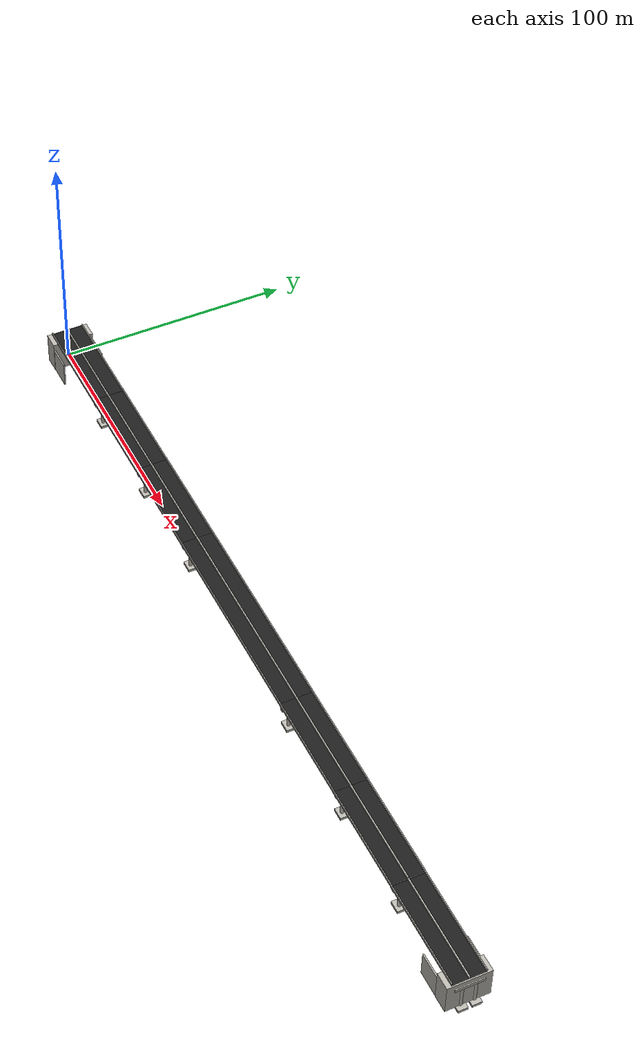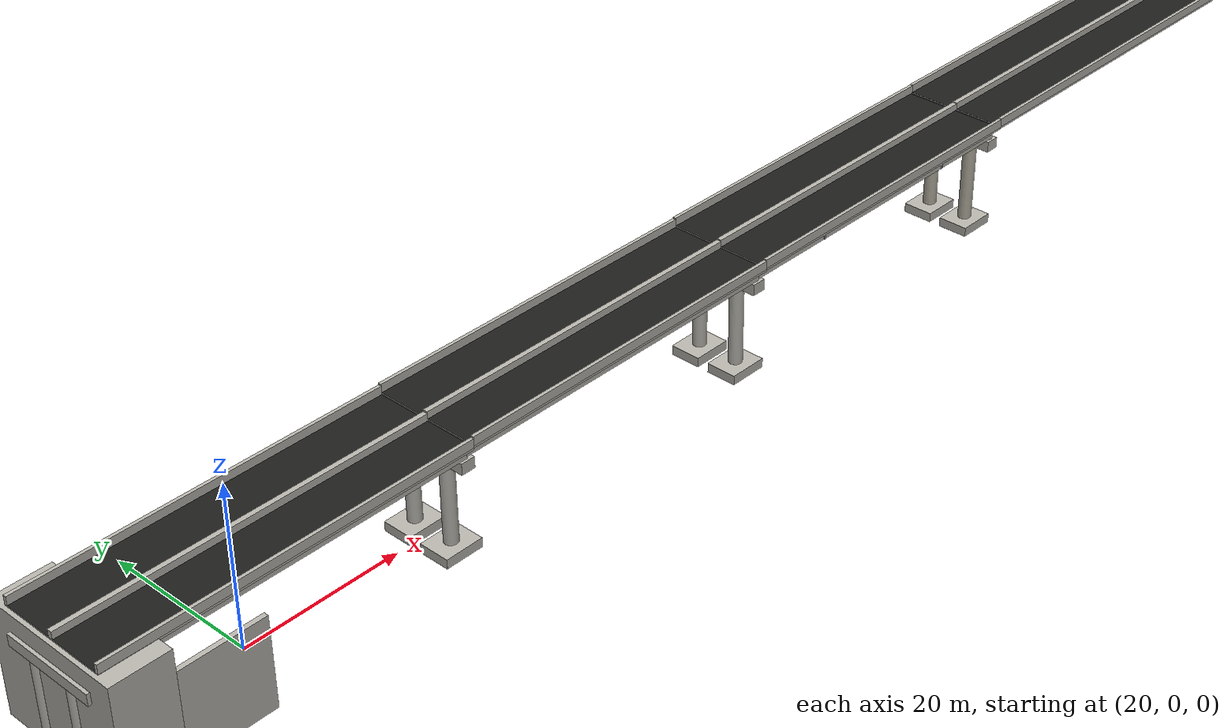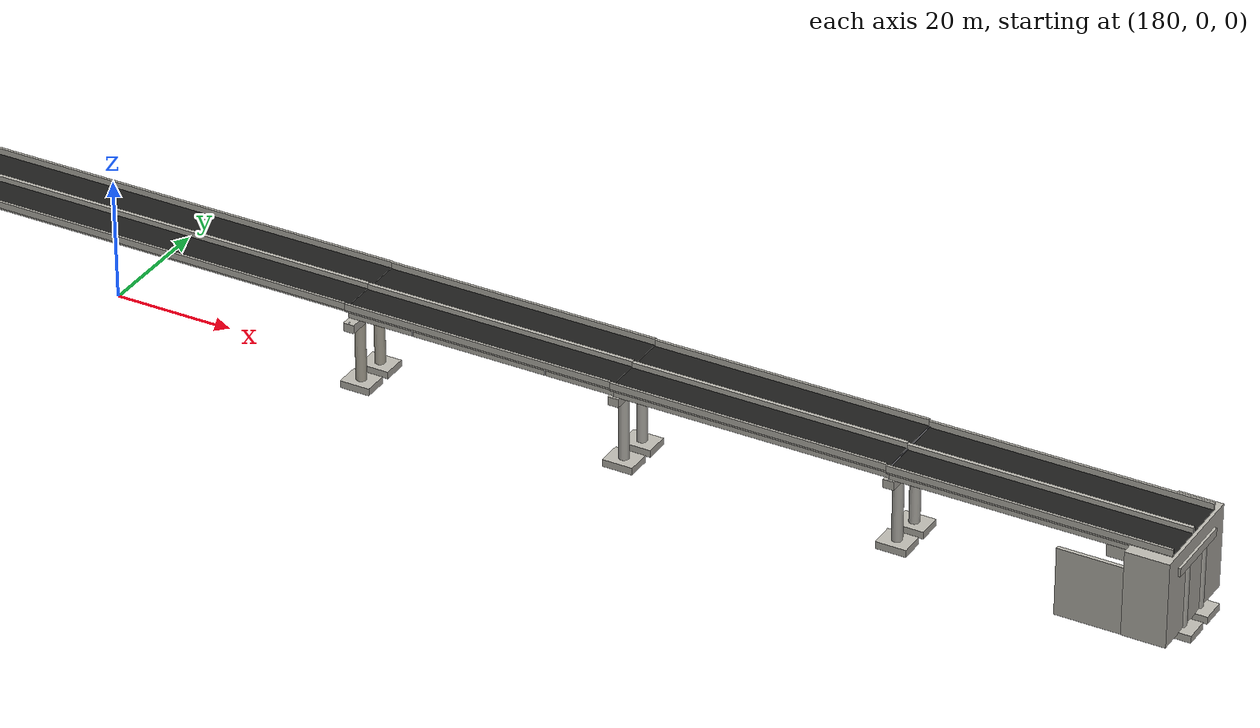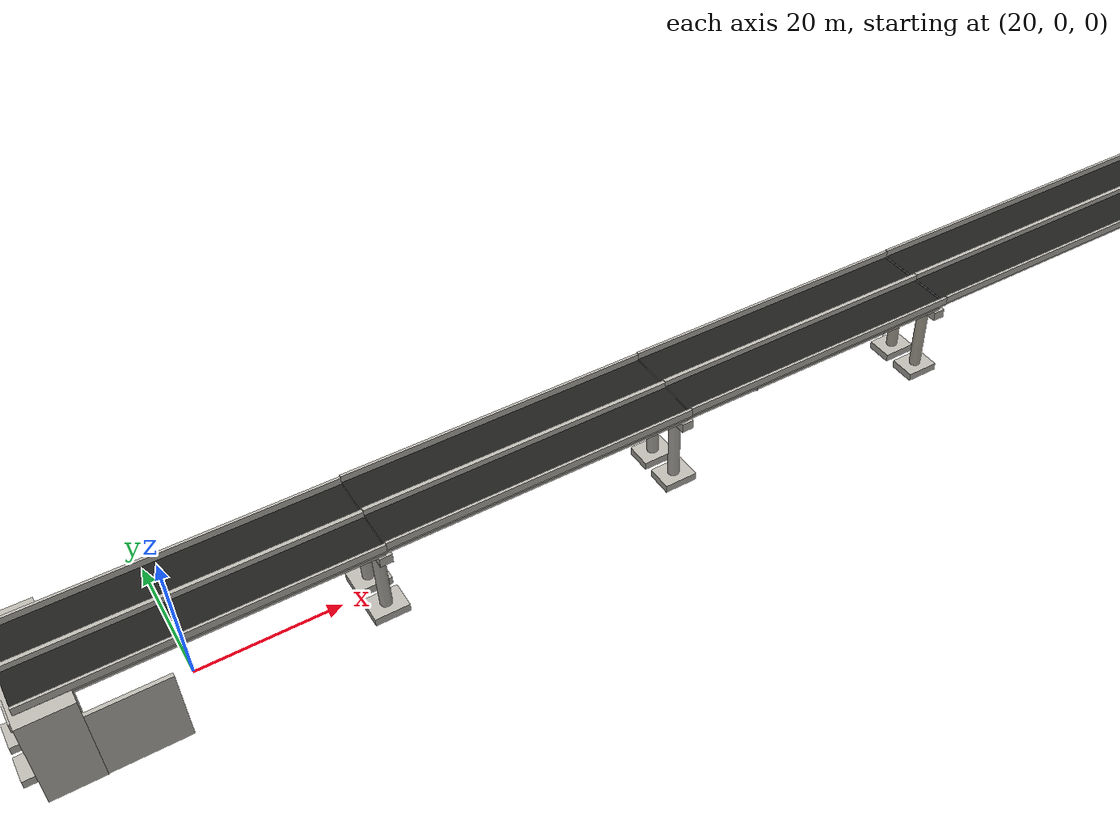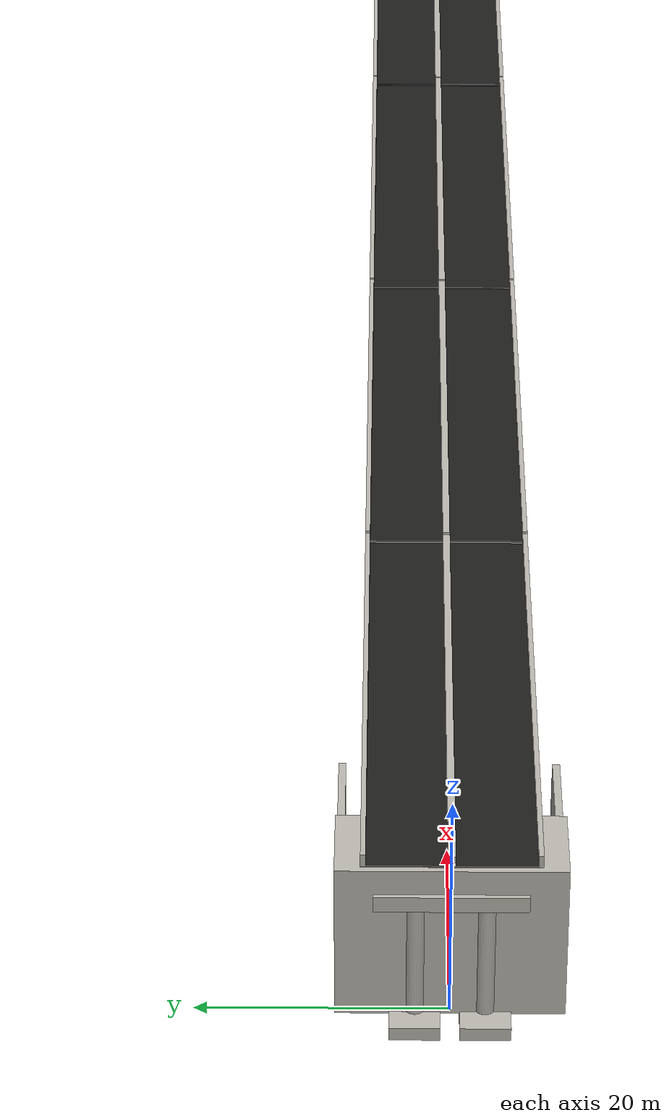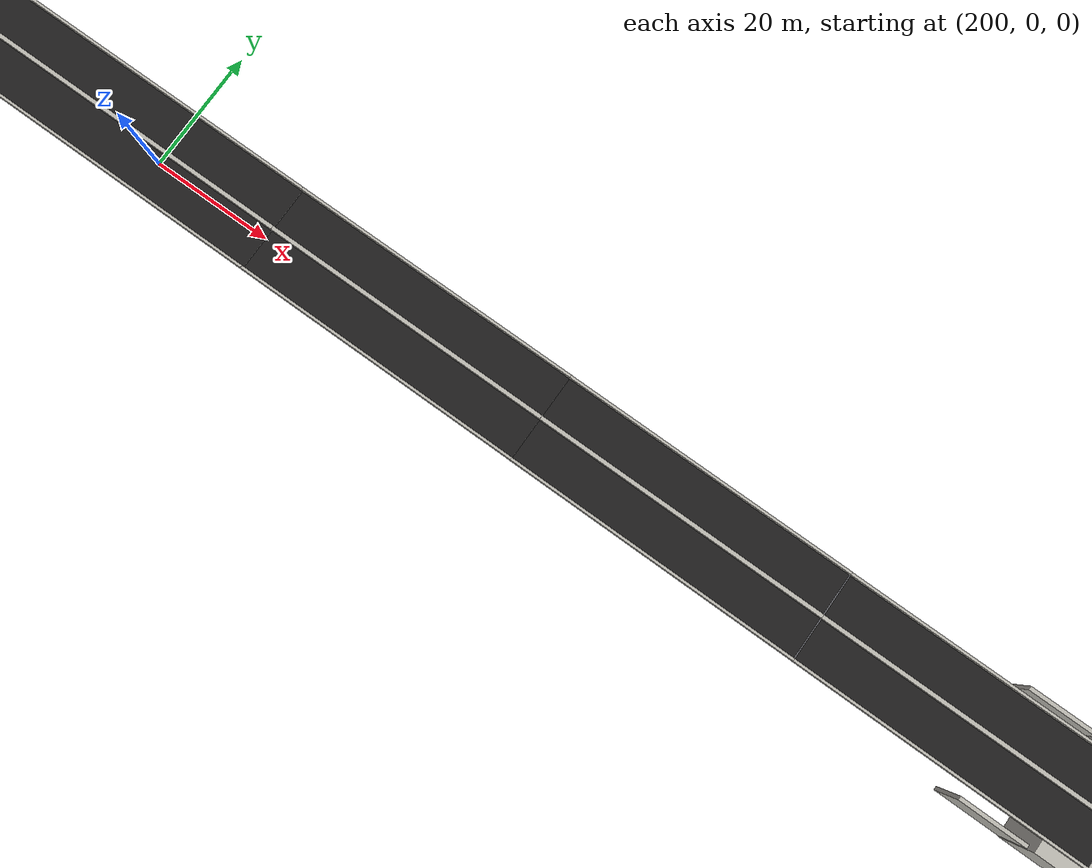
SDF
<?xml version="1.0" ?>
<sdf version="1.9">
  <model name="avian_final_road">
    <static>true</static>
    <pose>0 0 0 0 0 0</pose>
    <link name="link">
      <collision name="BR_ABUTMENT_NORTH_collision">
        <pose>357.000000 0.000000 7.000000 0 0 0.000000</pose>
        <geometry>
          <box>
            <size>7.000000 18.000000 14.000000</size>
          </box>
        </geometry>
      </collision>
      <visual name="BR_ABUTMENT_NORTH_visual">
        <pose>357.000000 0.000000 7.000000 0 0 0.000000</pose>
        <geometry>
          <box>
            <size>7.000000 18.000000 14.000000</size>
          </box>
        </geometry>
        <material>
          <ambient>0.288 0.284 0.272 1</ambient>
          <diffuse>0.720 0.710 0.680 1</diffuse>
          <specular>0.1 0.1 0.1 1</specular>
        </material>
      </visual>
      <collision name="BR_ABUTMENT_SOUTH_collision">
        <pose>3.000000 0.000000 7.000000 0 0 0.000000</pose>
        <geometry>
          <box>
            <size>7.000000 18.000000 14.000000</size>
          </box>
        </geometry>
      </collision>
      <visual name="BR_ABUTMENT_SOUTH_visual">
        <pose>3.000000 0.000000 7.000000 0 0 0.000000</pose>
        <geometry>
          <box>
            <size>7.000000 18.000000 14.000000</size>
          </box>
        </geometry>
        <material>
          <ambient>0.288 0.284 0.272 1</ambient>
          <diffuse>0.720 0.710 0.680 1</diffuse>
          <specular>0.1 0.1 0.1 1</specular>
        </material>
      </visual>
      <collision name="BR_BEARING_001_G1_collision">
        <pose>0.000000 -5.500000 11.625000 0 0 0.000000</pose>
        <geometry>
          <box>
            <size>0.500000 0.450000 0.300000</size>
          </box>
        </geometry>
      </collision>
      <visual name="BR_BEARING_001_G1_visual">
        <pose>0.000000 -5.500000 11.625000 0 0 0.000000</pose>
        <geometry>
          <box>
            <size>0.500000 0.450000 0.300000</size>
          </box>
        </geometry>
        <material>
          <ambient>0.220 0.224 0.232 1</ambient>
          <diffuse>0.550 0.560 0.580 1</diffuse>
          <specular>0.1 0.1 0.1 1</specular>
        </material>
      </visual>
      <collision name="BR_BEARING_001_G2_collision">
        <pose>0.000000 -2.750000 11.625000 0 0 0.000000</pose>
        <geometry>
          <box>
            <size>0.500000 0.450000 0.300000</size>
          </box>
        </geometry>
      </collision>
      <visual name="BR_BEARING_001_G2_visual">
        <pose>0.000000 -2.750000 11.625000 0 0 0.000000</pose>
        <geometry>
          <box>
            <size>0.500000 0.450000 0.300000</size>
          </box>
        </geometry>
        <material>
          <ambient>0.220 0.224 0.232 1</ambient>
          <diffuse>0.550 0.560 0.580 1</diffuse>
          <specular>0.1 0.1 0.1 1</specular>
        </material>
      </visual>
      <collision name="BR_BEARING_001_G3_collision">
        <pose>0.000000 0.000000 11.625000 0 0 0.000000</pose>
        <geometry>
          <box>
            <size>0.500000 0.450000 0.300000</size>
          </box>
        </geometry>
      </collision>
      <visual name="BR_BEARING_001_G3_visual">
        <pose>0.000000 0.000000 11.625000 0 0 0.000000</pose>
        <geometry>
          <box>
            <size>0.500000 0.450000 0.300000</size>
          </box>
        </geometry>
        <material>
          <ambient>0.220 0.224 0.232 1</ambient>
          <diffuse>0.550 0.560 0.580 1</diffuse>
          <specular>0.1 0.1 0.1 1</specular>
        </material>
      </visual>
      <collision name="BR_BEARING_001_G4_collision">
        <pose>0.000000 2.750000 11.625000 0 0 0.000000</pose>
        <geometry>
          <box>
            <size>0.500000 0.450000 0.300000</size>
          </box>
        </geometry>
      </collision>
      <visual name="BR_BEARING_001_G4_visual">
        <pose>0.000000 2.750000 11.625000 0 0 0.000000</pose>
        <geometry>
          <box>
            <size>0.500000 0.450000 0.300000</size>
          </box>
        </geometry>
        <material>
          <ambient>0.220 0.224 0.232 1</ambient>
          <diffuse>0.550 0.560 0.580 1</diffuse>
          <specular>0.1 0.1 0.1 1</specular>
        </material>
      </visual>
      <collision name="BR_BEARING_001_G5_collision">
        <pose>0.000000 5.500000 11.625000 0 0 0.000000</pose>
        <geometry>
          <box>
            <size>0.500000 0.450000 0.300000</size>
          </box>
        </geometry>
      </collision>
      <visual name="BR_BEARING_001_G5_visual">
        <pose>0.000000 5.500000 11.625000 0 0 0.000000</pose>
        <geometry>
          <box>
            <size>0.500000 0.450000 0.300000</size>
          </box>
        </geometry>
        <material>
          <ambient>0.220 0.224 0.232 1</ambient>
          <diffuse>0.550 0.560 0.580 1</diffuse>
          <specular>0.1 0.1 0.1 1</specular>
        </material>
      </visual>
      <collision name="BR_BEARING_002_G1_collision">
        <pose>45.000000 -5.500000 11.887500 0 0 0.000000</pose>
        <geometry>
          <box>
            <size>0.500000 0.450000 0.300000</size>
          </box>
        </geometry>
      </collision>
      <visual name="BR_BEARING_002_G1_visual">
        <pose>45.000000 -5.500000 11.887500 0 0 0.000000</pose>
        <geometry>
          <box>
            <size>0.500000 0.450000 0.300000</size>
          </box>
        </geometry>
        <material>
          <ambient>0.220 0.224 0.232 1</ambient>
          <diffuse>0.550 0.560 0.580 1</diffuse>
          <specular>0.1 0.1 0.1 1</specular>
        </material>
      </visual>
      <collision name="BR_BEARING_002_G2_collision">
        <pose>45.000000 -2.750000 11.887500 0 0 0.000000</pose>
        <geometry>
          <box>
            <size>0.500000 0.450000 0.300000</size>
          </box>
        </geometry>
      </collision>
      <visual name="BR_BEARING_002_G2_visual">
        <pose>45.000000 -2.750000 11.887500 0 0 0.000000</pose>
        <geometry>
          <box>
            <size>0.500000 0.450000 0.300000</size>
          </box>
        </geometry>
        <material>
          <ambient>0.220 0.224 0.232 1</ambient>
          <diffuse>0.550 0.560 0.580 1</diffuse>
          <specular>0.1 0.1 0.1 1</specular>
        </material>
      </visual>
      <collision name="BR_BEARING_002_G3_collision">
        <pose>45.000000 0.000000 11.887500 0 0 0.000000</pose>
        <geometry>
          <box>
            <size>0.500000 0.450000 0.300000</size>
          </box>
        </geometry>
      </collision>
      <visual name="BR_BEARING_002_G3_visual">
        <pose>45.000000 0.000000 11.887500 0 0 0.000000</pose>
        <geometry>
          <box>
            <size>0.500000 0.450000 0.300000</size>
          </box>
        </geometry>
        <material>
          <ambient>0.220 0.224 0.232 1</ambient>
          <diffuse>0.550 0.560 0.580 1</diffuse>
          <specular>0.1 0.1 0.1 1</specular>
        </material>
      </visual>
      <collision name="BR_BEARING_002_G4_collision">
        <pose>45.000000 2.750000 11.887500 0 0 0.000000</pose>
        <geometry>
          <box>
            <size>0.500000 0.450000 0.300000</size>
          </box>
        </geometry>
      </collision>
      <visual name="BR_BEARING_002_G4_visual">
        <pose>45.000000 2.750000 11.887500 0 0 0.000000</pose>
        <geometry>
          <box>
            <size>0.500000 0.450000 0.300000</size>
          </box>
        </geometry>
        <material>
          <ambient>0.220 0.224 0.232 1</ambient>
          <diffuse>0.550 0.560 0.580 1</diffuse>
          <specular>0.1 0.1 0.1 1</specular>
        </material>
      </visual>
      <collision name="BR_BEARING_002_G5_collision">
        <pose>45.000000 5.500000 11.887500 0 0 0.000000</pose>
        <geometry>
          <box>
            <size>0.500000 0.450000 0.300000</size>
          </box>
        </geometry>
      </collision>
      <visual name="BR_BEARING_002_G5_visual">
        <pose>45.000000 5.500000 11.887500 0 0 0.000000</pose>
        <geometry>
          <box>
            <size>0.500000 0.450000 0.300000</size>
          </box>
        </geometry>
        <material>
          <ambient>0.220 0.224 0.232 1</ambient>
          <diffuse>0.550 0.560 0.580 1</diffuse>
          <specular>0.1 0.1 0.1 1</specular>
        </material>
      </visual>
      <collision name="BR_BEARING_003_G1_collision">
        <pose>90.000000 -5.500000 12.075000 0 0 0.000000</pose>
        <geometry>
          <box>
            <size>0.500000 0.450000 0.300000</size>
          </box>
        </geometry>
      </collision>
      <visual name="BR_BEARING_003_G1_visual">
        <pose>90.000000 -5.500000 12.075000 0 0 0.000000</pose>
        <geometry>
          <box>
            <size>0.500000 0.450000 0.300000</size>
          </box>
        </geometry>
        <material>
          <ambient>0.220 0.224 0.232 1</ambient>
          <diffuse>0.550 0.560 0.580 1</diffuse>
          <specular>0.1 0.1 0.1 1</specular>
        </material>
      </visual>
      <collision name="BR_BEARING_003_G2_collision">
        <pose>90.000000 -2.750000 12.075000 0 0 0.000000</pose>
        <geometry>
          <box>
            <size>0.500000 0.450000 0.300000</size>
          </box>
        </geometry>
      </collision>
      <visual name="BR_BEARING_003_G2_visual">
        <pose>90.000000 -2.750000 12.075000 0 0 0.000000</pose>
        <geometry>
          <box>
            <size>0.500000 0.450000 0.300000</size>
          </box>
        </geometry>
        <material>
          <ambient>0.220 0.224 0.232 1</ambient>
          <diffuse>0.550 0.560 0.580 1</diffuse>
          <specular>0.1 0.1 0.1 1</specular>
        </material>
      </visual>
      <collision name="BR_BEARING_003_G3_collision">
        <pose>90.000000 0.000000 12.075000 0 0 0.000000</pose>
        <geometry>
          <box>
            <size>0.500000 0.450000 0.300000</size>
          </box>
        </geometry>
      </collision>
      <visual name="BR_BEARING_003_G3_visual">
        <pose>90.000000 0.000000 12.075000 0 0 0.000000</pose>
        <geometry>
          <box>
            <size>0.500000 0.450000 0.300000</size>
          </box>
        </geometry>
        <material>
          <ambient>0.220 0.224 0.232 1</ambient>
          <diffuse>0.550 0.560 0.580 1</diffuse>
          <specular>0.1 0.1 0.1 1</specular>
        </material>
      </visual>
      <collision name="BR_BEARING_003_G4_collision">
        <pose>90.000000 2.750000 12.075000 0 0 0.000000</pose>
        <geometry>
          <box>
            <size>0.500000 0.450000 0.300000</size>
          </box>
        </geometry>
      </collision>
      <visual name="BR_BEARING_003_G4_visual">
        <pose>90.000000 2.750000 12.075000 0 0 0.000000</pose>
        <geometry>
          <box>
            <size>0.500000 0.450000 0.300000</size>
          </box>
        </geometry>
        <material>
          <ambient>0.220 0.224 0.232 1</ambient>
          <diffuse>0.550 0.560 0.580 1</diffuse>
          <specular>0.1 0.1 0.1 1</specular>
        </material>
      </visual>
      <collision name="BR_BEARING_003_G5_collision">
        <pose>90.000000 5.500000 12.075000 0 0 0.000000</pose>
        <geometry>
          <box>
            <size>0.500000 0.450000 0.300000</size>
          </box>
        </geometry>
      </collision>
      <visual name="BR_BEARING_003_G5_visual">
        <pose>90.000000 5.500000 12.075000 0 0 0.000000</pose>
        <geometry>
          <box>
            <size>0.500000 0.450000 0.300000</size>
          </box>
        </geometry>
        <material>
          <ambient>0.220 0.224 0.232 1</ambient>
          <diffuse>0.550 0.560 0.580 1</diffuse>
          <specular>0.1 0.1 0.1 1</specular>
        </material>
      </visual>
      <collision name="BR_BEARING_004_G1_collision">
        <pose>135.000000 -5.500000 12.187500 0 0 0.000000</pose>
        <geometry>
          <box>
            <size>0.500000 0.450000 0.300000</size>
          </box>
        </geometry>
      </collision>
      <visual name="BR_BEARING_004_G1_visual">
        <pose>135.000000 -5.500000 12.187500 0 0 0.000000</pose>
        <geometry>
          <box>
            <size>0.500000 0.450000 0.300000</size>
          </box>
        </geometry>
        <material>
          <ambient>0.220 0.224 0.232 1</ambient>
          <diffuse>0.550 0.560 0.580 1</diffuse>
          <specular>0.1 0.1 0.1 1</specular>
        </material>
      </visual>
      <collision name="BR_BEARING_004_G2_collision">
        <pose>135.000000 -2.750000 12.187500 0 0 0.000000</pose>
        <geometry>
          <box>
            <size>0.500000 0.450000 0.300000</size>
          </box>
        </geometry>
      </collision>
      <visual name="BR_BEARING_004_G2_visual">
        <pose>135.000000 -2.750000 12.187500 0 0 0.000000</pose>
        <geometry>
          <box>
            <size>0.500000 0.450000 0.300000</size>
          </box>
        </geometry>
        <material>
          <ambient>0.220 0.224 0.232 1</ambient>
          <diffuse>0.550 0.560 0.580 1</diffuse>
          <specular>0.1 0.1 0.1 1</specular>
        </material>
      </visual>
      <collision name="BR_BEARING_004_G3_collision">
        <pose>135.000000 0.000000 12.187500 0 0 0.000000</pose>
        <geometry>
          <box>
            <size>0.500000 0.450000 0.300000</size>
          </box>
        </geometry>
      </collision>
      <visual name="BR_BEARING_004_G3_visual">
        <pose>135.000000 0.000000 12.187500 0 0 0.000000</pose>
        <geometry>
          <box>
            <size>0.500000 0.450000 0.300000</size>
          </box>
        </geometry>
        <material>
          <ambient>0.220 0.224 0.232 1</ambient>
          <diffuse>0.550 0.560 0.580 1</diffuse>
          <specular>0.1 0.1 0.1 1</specular>
        </material>
      </visual>
      <collision name="BR_BEARING_004_G4_collision">
        <pose>135.000000 2.750000 12.187500 0 0 0.000000</pose>
        <geometry>
          <box>
            <size>0.500000 0.450000 0.300000</size>
          </box>
        </geometry>
      </collision>
      <visual name="BR_BEARING_004_G4_visual">
        <pose>135.000000 2.750000 12.187500 0 0 0.000000</pose>
        <geometry>
          <box>
            <size>0.500000 0.450000 0.300000</size>
          </box>
        </geometry>
        <material>
          <ambient>0.220 0.224 0.232 1</ambient>
          <diffuse>0.550 0.560 0.580 1</diffuse>
          <specular>0.1 0.1 0.1 1</specular>
        </material>
      </visual>
      <collision name="BR_BEARING_004_G5_collision">
        <pose>135.000000 5.500000 12.187500 0 0 0.000000</pose>
        <geometry>
          <box>
            <size>0.500000 0.450000 0.300000</size>
          </box>
        </geometry>
      </collision>
      <visual name="BR_BEARING_004_G5_visual">
        <pose>135.000000 5.500000 12.187500 0 0 0.000000</pose>
        <geometry>
          <box>
            <size>0.500000 0.450000 0.300000</size>
          </box>
        </geometry>
        <material>
          <ambient>0.220 0.224 0.232 1</ambient>
          <diffuse>0.550 0.560 0.580 1</diffuse>
          <specular>0.1 0.1 0.1 1</specular>
        </material>
      </visual>
      <collision name="BR_BEARING_005_G1_collision">
        <pose>225.000000 -5.500000 11.287500 0 0 0.000000</pose>
        <geometry>
          <box>
            <size>0.500000 0.450000 0.300000</size>
          </box>
        </geometry>
      </collision>
      <visual name="BR_BEARING_005_G1_visual">
        <pose>225.000000 -5.500000 11.287500 0 0 0.000000</pose>
        <geometry>
          <box>
            <size>0.500000 0.450000 0.300000</size>
          </box>
        </geometry>
        <material>
          <ambient>0.220 0.224 0.232 1</ambient>
          <diffuse>0.550 0.560 0.580 1</diffuse>
          <specular>0.1 0.1 0.1 1</specular>
        </material>
      </visual>
      <collision name="BR_BEARING_005_G2_collision">
        <pose>225.000000 -2.750000 11.287500 0 0 0.000000</pose>
        <geometry>
          <box>
            <size>0.500000 0.450000 0.300000</size>
          </box>
        </geometry>
      </collision>
      <visual name="BR_BEARING_005_G2_visual">
        <pose>225.000000 -2.750000 11.287500 0 0 0.000000</pose>
        <geometry>
          <box>
            <size>0.500000 0.450000 0.300000</size>
          </box>
        </geometry>
        <material>
          <ambient>0.220 0.224 0.232 1</ambient>
          <diffuse>0.550 0.560 0.580 1</diffuse>
          <specular>0.1 0.1 0.1 1</specular>
        </material>
      </visual>
      <collision name="BR_BEARING_005_G3_collision">
        <pose>225.000000 0.000000 11.287500 0 0 0.000000</pose>
        <geometry>
          <box>
            <size>0.500000 0.450000 0.300000</size>
          </box>
        </geometry>
      </collision>
      <visual name="BR_BEARING_005_G3_visual">
        <pose>225.000000 0.000000 11.287500 0 0 0.000000</pose>
        <geometry>
          <box>
            <size>0.500000 0.450000 0.300000</size>
          </box>
        </geometry>
        <material>
          <ambient>0.220 0.224 0.232 1</ambient>
          <diffuse>0.550 0.560 0.580 1</diffuse>
          <specular>0.1 0.1 0.1 1</specular>
        </material>
      </visual>
      <collision name="BR_BEARING_005_G4_collision">
        <pose>225.000000 2.750000 11.287500 0 0 0.000000</pose>
        <geometry>
          <box>
            <size>0.500000 0.450000 0.300000</size>
          </box>
        </geometry>
      </collision>
      <visual name="BR_BEARING_005_G4_visual">
        <pose>225.000000 2.750000 11.287500 0 0 0.000000</pose>
        <geometry>
          <box>
            <size>0.500000 0.450000 0.300000</size>
          </box>
        </geometry>
        <material>
          <ambient>0.220 0.224 0.232 1</ambient>
          <diffuse>0.550 0.560 0.580 1</diffuse>
          <specular>0.1 0.1 0.1 1</specular>
        </material>
      </visual>
      <collision name="BR_BEARING_005_G5_collision">
        <pose>225.000000 5.500000 11.287500 0 0 0.000000</pose>
        <geometry>
          <box>
            <size>0.500000 0.450000 0.300000</size>
          </box>
        </geometry>
      </collision>
      <visual name="BR_BEARING_005_G5_visual">
        <pose>225.000000 5.500000 11.287500 0 0 0.000000</pose>
        <geometry>
          <box>
            <size>0.500000 0.450000 0.300000</size>
          </box>
        </geometry>
        <material>
          <ambient>0.220 0.224 0.232 1</ambient>
          <diffuse>0.550 0.560 0.580 1</diffuse>
          <specular>0.1 0.1 0.1 1</specular>
        </material>
      </visual>
      <collision name="BR_BEARING_006_G1_collision">
        <pose>270.000000 -5.500000 12.075000 0 0 0.000000</pose>
        <geometry>
          <box>
            <size>0.500000 0.450000 0.300000</size>
          </box>
        </geometry>
      </collision>
      <visual name="BR_BEARING_006_G1_visual">
        <pose>270.000000 -5.500000 12.075000 0 0 0.000000</pose>
        <geometry>
          <box>
            <size>0.500000 0.450000 0.300000</size>
          </box>
        </geometry>
        <material>
          <ambient>0.220 0.224 0.232 1</ambient>
          <diffuse>0.550 0.560 0.580 1</diffuse>
          <specular>0.1 0.1 0.1 1</specular>
        </material>
      </visual>
      <collision name="BR_BEARING_006_G2_collision">
        <pose>270.000000 -2.750000 12.075000 0 0 0.000000</pose>
        <geometry>
          <box>
            <size>0.500000 0.450000 0.300000</size>
          </box>
        </geometry>
      </collision>
      <visual name="BR_BEARING_006_G2_visual">
        <pose>270.000000 -2.750000 12.075000 0 0 0.000000</pose>
        <geometry>
          <box>
            <size>0.500000 0.450000 0.300000</size>
          </box>
        </geometry>
        <material>
          <ambient>0.220 0.224 0.232 1</ambient>
          <diffuse>0.550 0.560 0.580 1</diffuse>
          <specular>0.1 0.1 0.1 1</specular>
        </material>
      </visual>
      <collision name="BR_BEARING_006_G3_collision">
        <pose>270.000000 0.000000 12.075000 0 0 0.000000</pose>
        <geometry>
          <box>
            <size>0.500000 0.450000 0.300000</size>
          </box>
        </geometry>
      </collision>
      <visual name="BR_BEARING_006_G3_visual">
        <pose>270.000000 0.000000 12.075000 0 0 0.000000</pose>
        <geometry>
          <box>
            <size>0.500000 0.450000 0.300000</size>
          </box>
        </geometry>
        <material>
          <ambient>0.220 0.224 0.232 1</ambient>
          <diffuse>0.550 0.560 0.580 1</diffuse>
          <specular>0.1 0.1 0.1 1</specular>
        </material>
      </visual>
      <collision name="BR_BEARING_006_G4_collision">
        <pose>270.000000 2.750000 12.075000 0 0 0.000000</pose>
        <geometry>
          <box>
            <size>0.500000 0.450000 0.300000</size>
          </box>
        </geometry>
      </collision>
      <visual name="BR_BEARING_006_G4_visual">
        <pose>270.000000 2.750000 12.075000 0 0 0.000000</pose>
        <geometry>
          <box>
            <size>0.500000 0.450000 0.300000</size>
          </box>
        </geometry>
        <material>
          <ambient>0.220 0.224 0.232 1</ambient>
          <diffuse>0.550 0.560 0.580 1</diffuse>
          <specular>0.1 0.1 0.1 1</specular>
        </material>
      </visual>
      <collision name="BR_BEARING_006_G5_collision">
        <pose>270.000000 5.500000 12.075000 0 0 0.000000</pose>
        <geometry>
          <box>
            <size>0.500000 0.450000 0.300000</size>
          </box>
        </geometry>
      </collision>
      <visual name="BR_BEARING_006_G5_visual">
        <pose>270.000000 5.500000 12.075000 0 0 0.000000</pose>
        <geometry>
          <box>
            <size>0.500000 0.450000 0.300000</size>
          </box>
        </geometry>
        <material>
          <ambient>0.220 0.224 0.232 1</ambient>
          <diffuse>0.550 0.560 0.580 1</diffuse>
          <specular>0.1 0.1 0.1 1</specular>
        </material>
      </visual>
      <collision name="BR_BEARING_007_G1_collision">
        <pose>315.000000 -5.500000 11.887500 0 0 0.000000</pose>
        <geometry>
          <box>
            <size>0.500000 0.450000 0.300000</size>
          </box>
        </geometry>
      </collision>
      <visual name="BR_BEARING_007_G1_visual">
        <pose>315.000000 -5.500000 11.887500 0 0 0.000000</pose>
        <geometry>
          <box>
            <size>0.500000 0.450000 0.300000</size>
          </box>
        </geometry>
        <material>
          <ambient>0.220 0.224 0.232 1</ambient>
          <diffuse>0.550 0.560 0.580 1</diffuse>
          <specular>0.1 0.1 0.1 1</specular>
        </material>
      </visual>
      <collision name="BR_BEARING_007_G2_collision">
        <pose>315.000000 -2.750000 11.887500 0 0 0.000000</pose>
        <geometry>
          <box>
            <size>0.500000 0.450000 0.300000</size>
          </box>
        </geometry>
      </collision>
      <visual name="BR_BEARING_007_G2_visual">
        <pose>315.000000 -2.750000 11.887500 0 0 0.000000</pose>
        <geometry>
          <box>
            <size>0.500000 0.450000 0.300000</size>
          </box>
        </geometry>
        <material>
          <ambient>0.220 0.224 0.232 1</ambient>
          <diffuse>0.550 0.560 0.580 1</diffuse>
          <specular>0.1 0.1 0.1 1</specular>
        </material>
      </visual>
      <collision name="BR_BEARING_007_G3_collision">
        <pose>315.000000 0.000000 11.887500 0 0 0.000000</pose>
        <geometry>
          <box>
            <size>0.500000 0.450000 0.300000</size>
          </box>
        </geometry>
      </collision>
      <visual name="BR_BEARING_007_G3_visual">
        <pose>315.000000 0.000000 11.887500 0 0 0.000000</pose>
        <geometry>
          <box>
            <size>0.500000 0.450000 0.300000</size>
          </box>
        </geometry>
        <material>
          <ambient>0.220 0.224 0.232 1</ambient>
          <diffuse>0.550 0.560 0.580 1</diffuse>
          <specular>0.1 0.1 0.1 1</specular>
        </material>
      </visual>
      <collision name="BR_BEARING_007_G4_collision">
        <pose>315.000000 2.750000 11.887500 0 0 0.000000</pose>
        <geometry>
          <box>
            <size>0.500000 0.450000 0.300000</size>
          </box>
        </geometry>
      </collision>
      <visual name="BR_BEARING_007_G4_visual">
        <pose>315.000000 2.750000 11.887500 0 0 0.000000</pose>
        <geometry>
          <box>
            <size>0.500000 0.450000 0.300000</size>
          </box>
        </geometry>
        <material>
          <ambient>0.220 0.224 0.232 1</ambient>
          <diffuse>0.550 0.560 0.580 1</diffuse>
          <specular>0.1 0.1 0.1 1</specular>
        </material>
      </visual>
      <collision name="BR_BEARING_007_G5_collision">
        <pose>315.000000 5.500000 11.887500 0 0 0.000000</pose>
        <geometry>
          <box>
            <size>0.500000 0.450000 0.300000</size>
          </box>
        </geometry>
      </collision>
      <visual name="BR_BEARING_007_G5_visual">
        <pose>315.000000 5.500000 11.887500 0 0 0.000000</pose>
        <geometry>
          <box>
            <size>0.500000 0.450000 0.300000</size>
          </box>
        </geometry>
        <material>
          <ambient>0.220 0.224 0.232 1</ambient>
          <diffuse>0.550 0.560 0.580 1</diffuse>
          <specular>0.1 0.1 0.1 1</specular>
        </material>
      </visual>
      <collision name="BR_BEARING_008_G1_collision">
        <pose>360.000000 -5.500000 11.625000 0 0 0.000000</pose>
        <geometry>
          <box>
            <size>0.500000 0.450000 0.300000</size>
          </box>
        </geometry>
      </collision>
      <visual name="BR_BEARING_008_G1_visual">
        <pose>360.000000 -5.500000 11.625000 0 0 0.000000</pose>
        <geometry>
          <box>
            <size>0.500000 0.450000 0.300000</size>
          </box>
        </geometry>
        <material>
          <ambient>0.220 0.224 0.232 1</ambient>
          <diffuse>0.550 0.560 0.580 1</diffuse>
          <specular>0.1 0.1 0.1 1</specular>
        </material>
      </visual>
      <collision name="BR_BEARING_008_G2_collision">
        <pose>360.000000 -2.750000 11.625000 0 0 0.000000</pose>
        <geometry>
          <box>
            <size>0.500000 0.450000 0.300000</size>
          </box>
        </geometry>
      </collision>
      <visual name="BR_BEARING_008_G2_visual">
        <pose>360.000000 -2.750000 11.625000 0 0 0.000000</pose>
        <geometry>
          <box>
            <size>0.500000 0.450000 0.300000</size>
          </box>
        </geometry>
        <material>
          <ambient>0.220 0.224 0.232 1</ambient>
          <diffuse>0.550 0.560 0.580 1</diffuse>
          <specular>0.1 0.1 0.1 1</specular>
        </material>
      </visual>
      <collision name="BR_BEARING_008_G3_collision">
        <pose>360.000000 0.000000 11.625000 0 0 0.000000</pose>
        <geometry>
          <box>
            <size>0.500000 0.450000 0.300000</size>
          </box>
        </geometry>
      </collision>
      <visual name="BR_BEARING_008_G3_visual">
        <pose>360.000000 0.000000 11.625000 0 0 0.000000</pose>
        <geometry>
          <box>
            <size>0.500000 0.450000 0.300000</size>
          </box>
        </geometry>
        <material>
          <ambient>0.220 0.224 0.232 1</ambient>
          <diffuse>0.550 0.560 0.580 1</diffuse>
          <specular>0.1 0.1 0.1 1</specular>
        </material>
      </visual>
      <collision name="BR_BEARING_008_G4_collision">
        <pose>360.000000 2.750000 11.625000 0 0 0.000000</pose>
        <geometry>
          <box>
            <size>0.500000 0.450000 0.300000</size>
          </box>
        </geometry>
      </collision>
      <visual name="BR_BEARING_008_G4_visual">
        <pose>360.000000 2.750000 11.625000 0 0 0.000000</pose>
        <geometry>
          <box>
            <size>0.500000 0.450000 0.300000</size>
          </box>
        </geometry>
        <material>
          <ambient>0.220 0.224 0.232 1</ambient>
          <diffuse>0.550 0.560 0.580 1</diffuse>
          <specular>0.1 0.1 0.1 1</specular>
        </material>
      </visual>
      <collision name="BR_BEARING_008_G5_collision">
        <pose>360.000000 5.500000 11.625000 0 0 0.000000</pose>
        <geometry>
          <box>
            <size>0.500000 0.450000 0.300000</size>
          </box>
        </geometry>
      </collision>
      <visual name="BR_BEARING_008_G5_visual">
        <pose>360.000000 5.500000 11.625000 0 0 0.000000</pose>
        <geometry>
          <box>
            <size>0.500000 0.450000 0.300000</size>
          </box>
        </geometry>
        <material>
          <ambient>0.220 0.224 0.232 1</ambient>
          <diffuse>0.550 0.560 0.580 1</diffuse>
          <specular>0.1 0.1 0.1 1</specular>
        </material>
      </visual>
      <collision name="BR_DECK_SLAB_001_collision">
        <pose>22.500000 0.000000 13.940600 0 0 0.000000</pose>
        <geometry>
          <box>
            <size>45.000000 14.000000 0.250000</size>
          </box>
        </geometry>
      </collision>
      <visual name="BR_DECK_SLAB_001_visual">
        <pose>22.500000 0.000000 13.940600 0 0 0.000000</pose>
        <geometry>
          <box>
            <size>45.000000 14.000000 0.250000</size>
          </box>
        </geometry>
        <material>
          <ambient>0.288 0.284 0.272 1</ambient>
          <diffuse>0.720 0.710 0.680 1</diffuse>
          <specular>0.1 0.1 0.1 1</specular>
        </material>
      </visual>
      <collision name="BR_DECK_SLAB_002_collision">
        <pose>67.500000 0.000000 14.165600 0 0 0.000000</pose>
        <geometry>
          <box>
            <size>45.000000 14.000000 0.250000</size>
          </box>
        </geometry>
      </collision>
      <visual name="BR_DECK_SLAB_002_visual">
        <pose>67.500000 0.000000 14.165600 0 0 0.000000</pose>
        <geometry>
          <box>
            <size>45.000000 14.000000 0.250000</size>
          </box>
        </geometry>
        <material>
          <ambient>0.288 0.284 0.272 1</ambient>
          <diffuse>0.720 0.710 0.680 1</diffuse>
          <specular>0.1 0.1 0.1 1</specular>
        </material>
      </visual>
      <collision name="BR_DECK_SLAB_003_collision">
        <pose>112.500000 0.000000 14.315600 0 0 0.000000</pose>
        <geometry>
          <box>
            <size>45.000000 14.000000 0.250000</size>
          </box>
        </geometry>
      </collision>
      <visual name="BR_DECK_SLAB_003_visual">
        <pose>112.500000 0.000000 14.315600 0 0 0.000000</pose>
        <geometry>
          <box>
            <size>45.000000 14.000000 0.250000</size>
          </box>
        </geometry>
        <material>
          <ambient>0.288 0.284 0.272 1</ambient>
          <diffuse>0.720 0.710 0.680 1</diffuse>
          <specular>0.1 0.1 0.1 1</specular>
        </material>
      </visual>
      <collision name="BR_DECK_SLAB_004_collision">
        <pose>180.000000 0.000000 14.400000 0 0 0.000000</pose>
        <geometry>
          <box>
            <size>90.000000 14.000000 0.250000</size>
          </box>
        </geometry>
      </collision>
      <visual name="BR_DECK_SLAB_004_visual">
        <pose>180.000000 0.000000 14.400000 0 0 0.000000</pose>
        <geometry>
          <box>
            <size>90.000000 14.000000 0.250000</size>
          </box>
        </geometry>
        <material>
          <ambient>0.288 0.284 0.272 1</ambient>
          <diffuse>0.720 0.710 0.680 1</diffuse>
          <specular>0.1 0.1 0.1 1</specular>
        </material>
      </visual>
      <collision name="BR_DECK_SLAB_005_collision">
        <pose>247.500000 0.000000 14.315600 0 0 0.000000</pose>
        <geometry>
          <box>
            <size>45.000000 14.000000 0.250000</size>
          </box>
        </geometry>
      </collision>
      <visual name="BR_DECK_SLAB_005_visual">
        <pose>247.500000 0.000000 14.315600 0 0 0.000000</pose>
        <geometry>
          <box>
            <size>45.000000 14.000000 0.250000</size>
          </box>
        </geometry>
        <material>
          <ambient>0.288 0.284 0.272 1</ambient>
          <diffuse>0.720 0.710 0.680 1</diffuse>
          <specular>0.1 0.1 0.1 1</specular>
        </material>
      </visual>
      <collision name="BR_DECK_SLAB_006_collision">
        <pose>292.500000 0.000000 14.165600 0 0 0.000000</pose>
        <geometry>
          <box>
            <size>45.000000 14.000000 0.250000</size>
          </box>
        </geometry>
      </collision>
      <visual name="BR_DECK_SLAB_006_visual">
        <pose>292.500000 0.000000 14.165600 0 0 0.000000</pose>
        <geometry>
          <box>
            <size>45.000000 14.000000 0.250000</size>
          </box>
        </geometry>
        <material>
          <ambient>0.288 0.284 0.272 1</ambient>
          <diffuse>0.720 0.710 0.680 1</diffuse>
          <specular>0.1 0.1 0.1 1</specular>
        </material>
      </visual>
      <collision name="BR_DECK_SLAB_007_collision">
        <pose>337.500000 0.000000 13.940600 0 0 0.000000</pose>
        <geometry>
          <box>
            <size>45.000000 14.000000 0.250000</size>
          </box>
        </geometry>
      </collision>
      <visual name="BR_DECK_SLAB_007_visual">
        <pose>337.500000 0.000000 13.940600 0 0 0.000000</pose>
        <geometry>
          <box>
            <size>45.000000 14.000000 0.250000</size>
          </box>
        </geometry>
        <material>
          <ambient>0.288 0.284 0.272 1</ambient>
          <diffuse>0.720 0.710 0.680 1</diffuse>
          <specular>0.1 0.1 0.1 1</specular>
        </material>
      </visual>
      <collision name="BR_DIAPHRAGM_001_1_collision">
        <pose>0.300000 0.000000 13.045600 0 0 0.000000</pose>
        <geometry>
          <box>
            <size>0.300000 11.000000 1.100000</size>
          </box>
        </geometry>
      </collision>
      <visual name="BR_DIAPHRAGM_001_1_visual">
        <pose>0.300000 0.000000 13.045600 0 0 0.000000</pose>
        <geometry>
          <box>
            <size>0.300000 11.000000 1.100000</size>
          </box>
        </geometry>
        <material>
          <ambient>0.288 0.284 0.272 1</ambient>
          <diffuse>0.720 0.710 0.680 1</diffuse>
          <specular>0.1 0.1 0.1 1</specular>
        </material>
      </visual>
      <collision name="BR_DIAPHRAGM_001_2_collision">
        <pose>15.000000 0.000000 13.045600 0 0 0.000000</pose>
        <geometry>
          <box>
            <size>0.300000 11.000000 1.100000</size>
          </box>
        </geometry>
      </collision>
      <visual name="BR_DIAPHRAGM_001_2_visual">
        <pose>15.000000 0.000000 13.045600 0 0 0.000000</pose>
        <geometry>
          <box>
            <size>0.300000 11.000000 1.100000</size>
          </box>
        </geometry>
        <material>
          <ambient>0.288 0.284 0.272 1</ambient>
          <diffuse>0.720 0.710 0.680 1</diffuse>
          <specular>0.1 0.1 0.1 1</specular>
        </material>
      </visual>
      <collision name="BR_DIAPHRAGM_001_3_collision">
        <pose>30.000000 0.000000 13.045600 0 0 0.000000</pose>
        <geometry>
          <box>
            <size>0.300000 11.000000 1.100000</size>
          </box>
        </geometry>
      </collision>
      <visual name="BR_DIAPHRAGM_001_3_visual">
        <pose>30.000000 0.000000 13.045600 0 0 0.000000</pose>
        <geometry>
          <box>
            <size>0.300000 11.000000 1.100000</size>
          </box>
        </geometry>
        <material>
          <ambient>0.288 0.284 0.272 1</ambient>
          <diffuse>0.720 0.710 0.680 1</diffuse>
          <specular>0.1 0.1 0.1 1</specular>
        </material>
      </visual>
      <collision name="BR_DIAPHRAGM_001_4_collision">
        <pose>44.700000 0.000000 13.045600 0 0 0.000000</pose>
        <geometry>
          <box>
            <size>0.300000 11.000000 1.100000</size>
          </box>
        </geometry>
      </collision>
      <visual name="BR_DIAPHRAGM_001_4_visual">
        <pose>44.700000 0.000000 13.045600 0 0 0.000000</pose>
        <geometry>
          <box>
            <size>0.300000 11.000000 1.100000</size>
          </box>
        </geometry>
        <material>
          <ambient>0.288 0.284 0.272 1</ambient>
          <diffuse>0.720 0.710 0.680 1</diffuse>
          <specular>0.1 0.1 0.1 1</specular>
        </material>
      </visual>
      <collision name="BR_DIAPHRAGM_002_1_collision">
        <pose>45.300000 0.000000 13.270600 0 0 0.000000</pose>
        <geometry>
          <box>
            <size>0.300000 11.000000 1.100000</size>
          </box>
        </geometry>
      </collision>
      <visual name="BR_DIAPHRAGM_002_1_visual">
        <pose>45.300000 0.000000 13.270600 0 0 0.000000</pose>
        <geometry>
          <box>
            <size>0.300000 11.000000 1.100000</size>
          </box>
        </geometry>
        <material>
          <ambient>0.288 0.284 0.272 1</ambient>
          <diffuse>0.720 0.710 0.680 1</diffuse>
          <specular>0.1 0.1 0.1 1</specular>
        </material>
      </visual>
      <collision name="BR_DIAPHRAGM_002_2_collision">
        <pose>60.000000 0.000000 13.270600 0 0 0.000000</pose>
        <geometry>
          <box>
            <size>0.300000 11.000000 1.100000</size>
          </box>
        </geometry>
      </collision>
      <visual name="BR_DIAPHRAGM_002_2_visual">
        <pose>60.000000 0.000000 13.270600 0 0 0.000000</pose>
        <geometry>
          <box>
            <size>0.300000 11.000000 1.100000</size>
          </box>
        </geometry>
        <material>
          <ambient>0.288 0.284 0.272 1</ambient>
          <diffuse>0.720 0.710 0.680 1</diffuse>
          <specular>0.1 0.1 0.1 1</specular>
        </material>
      </visual>
      <collision name="BR_DIAPHRAGM_002_3_collision">
        <pose>75.000000 0.000000 13.270600 0 0 0.000000</pose>
        <geometry>
          <box>
            <size>0.300000 11.000000 1.100000</size>
          </box>
        </geometry>
      </collision>
      <visual name="BR_DIAPHRAGM_002_3_visual">
        <pose>75.000000 0.000000 13.270600 0 0 0.000000</pose>
        <geometry>
          <box>
            <size>0.300000 11.000000 1.100000</size>
          </box>
        </geometry>
        <material>
          <ambient>0.288 0.284 0.272 1</ambient>
          <diffuse>0.720 0.710 0.680 1</diffuse>
          <specular>0.1 0.1 0.1 1</specular>
        </material>
      </visual>
      <collision name="BR_DIAPHRAGM_002_4_collision">
        <pose>89.700000 0.000000 13.270600 0 0 0.000000</pose>
        <geometry>
          <box>
            <size>0.300000 11.000000 1.100000</size>
          </box>
        </geometry>
      </collision>
      <visual name="BR_DIAPHRAGM_002_4_visual">
        <pose>89.700000 0.000000 13.270600 0 0 0.000000</pose>
        <geometry>
          <box>
            <size>0.300000 11.000000 1.100000</size>
          </box>
        </geometry>
        <material>
          <ambient>0.288 0.284 0.272 1</ambient>
          <diffuse>0.720 0.710 0.680 1</diffuse>
          <specular>0.1 0.1 0.1 1</specular>
        </material>
      </visual>
      <collision name="BR_DIAPHRAGM_003_1_collision">
        <pose>90.300000 0.000000 13.420600 0 0 0.000000</pose>
        <geometry>
          <box>
            <size>0.300000 11.000000 1.100000</size>
          </box>
        </geometry>
      </collision>
      <visual name="BR_DIAPHRAGM_003_1_visual">
        <pose>90.300000 0.000000 13.420600 0 0 0.000000</pose>
        <geometry>
          <box>
            <size>0.300000 11.000000 1.100000</size>
          </box>
        </geometry>
        <material>
          <ambient>0.288 0.284 0.272 1</ambient>
          <diffuse>0.720 0.710 0.680 1</diffuse>
          <specular>0.1 0.1 0.1 1</specular>
        </material>
      </visual>
      <collision name="BR_DIAPHRAGM_003_2_collision">
        <pose>105.000000 0.000000 13.420600 0 0 0.000000</pose>
        <geometry>
          <box>
            <size>0.300000 11.000000 1.100000</size>
          </box>
        </geometry>
      </collision>
      <visual name="BR_DIAPHRAGM_003_2_visual">
        <pose>105.000000 0.000000 13.420600 0 0 0.000000</pose>
        <geometry>
          <box>
            <size>0.300000 11.000000 1.100000</size>
          </box>
        </geometry>
        <material>
          <ambient>0.288 0.284 0.272 1</ambient>
          <diffuse>0.720 0.710 0.680 1</diffuse>
          <specular>0.1 0.1 0.1 1</specular>
        </material>
      </visual>
      <collision name="BR_DIAPHRAGM_003_3_collision">
        <pose>120.000000 0.000000 13.420600 0 0 0.000000</pose>
        <geometry>
          <box>
            <size>0.300000 11.000000 1.100000</size>
          </box>
        </geometry>
      </collision>
      <visual name="BR_DIAPHRAGM_003_3_visual">
        <pose>120.000000 0.000000 13.420600 0 0 0.000000</pose>
        <geometry>
          <box>
            <size>0.300000 11.000000 1.100000</size>
          </box>
        </geometry>
        <material>
          <ambient>0.288 0.284 0.272 1</ambient>
          <diffuse>0.720 0.710 0.680 1</diffuse>
          <specular>0.1 0.1 0.1 1</specular>
        </material>
      </visual>
      <collision name="BR_DIAPHRAGM_003_4_collision">
        <pose>134.700000 0.000000 13.420600 0 0 0.000000</pose>
        <geometry>
          <box>
            <size>0.300000 11.000000 1.100000</size>
          </box>
        </geometry>
      </collision>
      <visual name="BR_DIAPHRAGM_003_4_visual">
        <pose>134.700000 0.000000 13.420600 0 0 0.000000</pose>
        <geometry>
          <box>
            <size>0.300000 11.000000 1.100000</size>
          </box>
        </geometry>
        <material>
          <ambient>0.288 0.284 0.272 1</ambient>
          <diffuse>0.720 0.710 0.680 1</diffuse>
          <specular>0.1 0.1 0.1 1</specular>
        </material>
      </visual>
      <collision name="BR_DIAPHRAGM_005_1_collision">
        <pose>225.300000 0.000000 13.420600 0 0 0.000000</pose>
        <geometry>
          <box>
            <size>0.300000 11.000000 1.100000</size>
          </box>
        </geometry>
      </collision>
      <visual name="BR_DIAPHRAGM_005_1_visual">
        <pose>225.300000 0.000000 13.420600 0 0 0.000000</pose>
        <geometry>
          <box>
            <size>0.300000 11.000000 1.100000</size>
          </box>
        </geometry>
        <material>
          <ambient>0.288 0.284 0.272 1</ambient>
          <diffuse>0.720 0.710 0.680 1</diffuse>
          <specular>0.1 0.1 0.1 1</specular>
        </material>
      </visual>
      <collision name="BR_DIAPHRAGM_005_2_collision">
        <pose>240.000000 0.000000 13.420600 0 0 0.000000</pose>
        <geometry>
          <box>
            <size>0.300000 11.000000 1.100000</size>
          </box>
        </geometry>
      </collision>
      <visual name="BR_DIAPHRAGM_005_2_visual">
        <pose>240.000000 0.000000 13.420600 0 0 0.000000</pose>
        <geometry>
          <box>
            <size>0.300000 11.000000 1.100000</size>
          </box>
        </geometry>
        <material>
          <ambient>0.288 0.284 0.272 1</ambient>
          <diffuse>0.720 0.710 0.680 1</diffuse>
          <specular>0.1 0.1 0.1 1</specular>
        </material>
      </visual>
      <collision name="BR_DIAPHRAGM_005_3_collision">
        <pose>255.000000 0.000000 13.420600 0 0 0.000000</pose>
        <geometry>
          <box>
            <size>0.300000 11.000000 1.100000</size>
          </box>
        </geometry>
      </collision>
      <visual name="BR_DIAPHRAGM_005_3_visual">
        <pose>255.000000 0.000000 13.420600 0 0 0.000000</pose>
        <geometry>
          <box>
            <size>0.300000 11.000000 1.100000</size>
          </box>
        </geometry>
        <material>
          <ambient>0.288 0.284 0.272 1</ambient>
          <diffuse>0.720 0.710 0.680 1</diffuse>
          <specular>0.1 0.1 0.1 1</specular>
        </material>
      </visual>
      <collision name="BR_DIAPHRAGM_005_4_collision">
        <pose>269.700000 0.000000 13.420600 0 0 0.000000</pose>
        <geometry>
          <box>
            <size>0.300000 11.000000 1.100000</size>
          </box>
        </geometry>
      </collision>
      <visual name="BR_DIAPHRAGM_005_4_visual">
        <pose>269.700000 0.000000 13.420600 0 0 0.000000</pose>
        <geometry>
          <box>
            <size>0.300000 11.000000 1.100000</size>
          </box>
        </geometry>
        <material>
          <ambient>0.288 0.284 0.272 1</ambient>
          <diffuse>0.720 0.710 0.680 1</diffuse>
          <specular>0.1 0.1 0.1 1</specular>
        </material>
      </visual>
      <collision name="BR_DIAPHRAGM_006_1_collision">
        <pose>270.300000 0.000000 13.270600 0 0 0.000000</pose>
        <geometry>
          <box>
            <size>0.300000 11.000000 1.100000</size>
          </box>
        </geometry>
      </collision>
      <visual name="BR_DIAPHRAGM_006_1_visual">
        <pose>270.300000 0.000000 13.270600 0 0 0.000000</pose>
        <geometry>
          <box>
            <size>0.300000 11.000000 1.100000</size>
          </box>
        </geometry>
        <material>
          <ambient>0.288 0.284 0.272 1</ambient>
          <diffuse>0.720 0.710 0.680 1</diffuse>
          <specular>0.1 0.1 0.1 1</specular>
        </material>
      </visual>
      <collision name="BR_DIAPHRAGM_006_2_collision">
        <pose>285.000000 0.000000 13.270600 0 0 0.000000</pose>
        <geometry>
          <box>
            <size>0.300000 11.000000 1.100000</size>
          </box>
        </geometry>
      </collision>
      <visual name="BR_DIAPHRAGM_006_2_visual">
        <pose>285.000000 0.000000 13.270600 0 0 0.000000</pose>
        <geometry>
          <box>
            <size>0.300000 11.000000 1.100000</size>
          </box>
        </geometry>
        <material>
          <ambient>0.288 0.284 0.272 1</ambient>
          <diffuse>0.720 0.710 0.680 1</diffuse>
          <specular>0.1 0.1 0.1 1</specular>
        </material>
      </visual>
      <collision name="BR_DIAPHRAGM_006_3_collision">
        <pose>300.000000 0.000000 13.270600 0 0 0.000000</pose>
        <geometry>
          <box>
            <size>0.300000 11.000000 1.100000</size>
          </box>
        </geometry>
      </collision>
      <visual name="BR_DIAPHRAGM_006_3_visual">
        <pose>300.000000 0.000000 13.270600 0 0 0.000000</pose>
        <geometry>
          <box>
            <size>0.300000 11.000000 1.100000</size>
          </box>
        </geometry>
        <material>
          <ambient>0.288 0.284 0.272 1</ambient>
          <diffuse>0.720 0.710 0.680 1</diffuse>
          <specular>0.1 0.1 0.1 1</specular>
        </material>
      </visual>
      <collision name="BR_DIAPHRAGM_006_4_collision">
        <pose>314.700000 0.000000 13.270600 0 0 0.000000</pose>
        <geometry>
          <box>
            <size>0.300000 11.000000 1.100000</size>
          </box>
        </geometry>
      </collision>
      <visual name="BR_DIAPHRAGM_006_4_visual">
        <pose>314.700000 0.000000 13.270600 0 0 0.000000</pose>
        <geometry>
          <box>
            <size>0.300000 11.000000 1.100000</size>
          </box>
        </geometry>
        <material>
          <ambient>0.288 0.284 0.272 1</ambient>
          <diffuse>0.720 0.710 0.680 1</diffuse>
          <specular>0.1 0.1 0.1 1</specular>
        </material>
      </visual>
      <collision name="BR_DIAPHRAGM_007_1_collision">
        <pose>315.300000 0.000000 13.045600 0 0 0.000000</pose>
        <geometry>
          <box>
            <size>0.300000 11.000000 1.100000</size>
          </box>
        </geometry>
      </collision>
      <visual name="BR_DIAPHRAGM_007_1_visual">
        <pose>315.300000 0.000000 13.045600 0 0 0.000000</pose>
        <geometry>
          <box>
            <size>0.300000 11.000000 1.100000</size>
          </box>
        </geometry>
        <material>
          <ambient>0.288 0.284 0.272 1</ambient>
          <diffuse>0.720 0.710 0.680 1</diffuse>
          <specular>0.1 0.1 0.1 1</specular>
        </material>
      </visual>
      <collision name="BR_DIAPHRAGM_007_2_collision">
        <pose>330.000000 0.000000 13.045600 0 0 0.000000</pose>
        <geometry>
          <box>
            <size>0.300000 11.000000 1.100000</size>
          </box>
        </geometry>
      </collision>
      <visual name="BR_DIAPHRAGM_007_2_visual">
        <pose>330.000000 0.000000 13.045600 0 0 0.000000</pose>
        <geometry>
          <box>
            <size>0.300000 11.000000 1.100000</size>
          </box>
        </geometry>
        <material>
          <ambient>0.288 0.284 0.272 1</ambient>
          <diffuse>0.720 0.710 0.680 1</diffuse>
          <specular>0.1 0.1 0.1 1</specular>
        </material>
      </visual>
      <collision name="BR_DIAPHRAGM_007_3_collision">
        <pose>345.000000 0.000000 13.045600 0 0 0.000000</pose>
        <geometry>
          <box>
            <size>0.300000 11.000000 1.100000</size>
          </box>
        </geometry>
      </collision>
      <visual name="BR_DIAPHRAGM_007_3_visual">
        <pose>345.000000 0.000000 13.045600 0 0 0.000000</pose>
        <geometry>
          <box>
            <size>0.300000 11.000000 1.100000</size>
          </box>
        </geometry>
        <material>
          <ambient>0.288 0.284 0.272 1</ambient>
          <diffuse>0.720 0.710 0.680 1</diffuse>
          <specular>0.1 0.1 0.1 1</specular>
        </material>
      </visual>
      <collision name="BR_DIAPHRAGM_007_4_collision">
        <pose>359.700000 0.000000 13.045600 0 0 0.000000</pose>
        <geometry>
          <box>
            <size>0.300000 11.000000 1.100000</size>
          </box>
        </geometry>
      </collision>
      <visual name="BR_DIAPHRAGM_007_4_visual">
        <pose>359.700000 0.000000 13.045600 0 0 0.000000</pose>
        <geometry>
          <box>
            <size>0.300000 11.000000 1.100000</size>
          </box>
        </geometry>
        <material>
          <ambient>0.288 0.284 0.272 1</ambient>
          <diffuse>0.720 0.710 0.680 1</diffuse>
          <specular>0.1 0.1 0.1 1</specular>
        </material>
      </visual>
      <collision name="BR_DRAIN_003_1L_collision">
        <pose>101.250000 6.300000 13.640600 0 0 0.000000</pose>
        <geometry>
          <box>
            <size>0.200000 0.190200 1.300000</size>
          </box>
        </geometry>
      </collision>
      <visual name="BR_DRAIN_003_1L_visual">
        <pose>101.250000 6.300000 13.640600 0 0 0.000000</pose>
        <geometry>
          <box>
            <size>0.200000 0.190200 1.300000</size>
          </box>
        </geometry>
        <material>
          <ambient>0.060 0.060 0.064 1</ambient>
          <diffuse>0.150 0.150 0.160 1</diffuse>
          <specular>0.1 0.1 0.1 1</specular>
        </material>
      </visual>
      <collision name="BR_DRAIN_003_1R_collision">
        <pose>101.250000 -6.300000 13.640600 0 0 0.000000</pose>
        <geometry>
          <box>
            <size>0.200000 0.190200 1.300000</size>
          </box>
        </geometry>
      </collision>
      <visual name="BR_DRAIN_003_1R_visual">
        <pose>101.250000 -6.300000 13.640600 0 0 0.000000</pose>
        <geometry>
          <box>
            <size>0.200000 0.190200 1.300000</size>
          </box>
        </geometry>
        <material>
          <ambient>0.060 0.060 0.064 1</ambient>
          <diffuse>0.150 0.150 0.160 1</diffuse>
          <specular>0.1 0.1 0.1 1</specular>
        </material>
      </visual>
      <collision name="BR_DRAIN_003_2L_collision">
        <pose>123.750000 6.300000 13.640600 0 0 0.000000</pose>
        <geometry>
          <box>
            <size>0.200000 0.190200 1.300000</size>
          </box>
        </geometry>
      </collision>
      <visual name="BR_DRAIN_003_2L_visual">
        <pose>123.750000 6.300000 13.640600 0 0 0.000000</pose>
        <geometry>
          <box>
            <size>0.200000 0.190200 1.300000</size>
          </box>
        </geometry>
        <material>
          <ambient>0.060 0.060 0.064 1</ambient>
          <diffuse>0.150 0.150 0.160 1</diffuse>
          <specular>0.1 0.1 0.1 1</specular>
        </material>
      </visual>
      <collision name="BR_DRAIN_003_2R_collision">
        <pose>123.750000 -6.300000 13.640600 0 0 0.000000</pose>
        <geometry>
          <box>
            <size>0.200000 0.190200 1.300000</size>
          </box>
        </geometry>
      </collision>
      <visual name="BR_DRAIN_003_2R_visual">
        <pose>123.750000 -6.300000 13.640600 0 0 0.000000</pose>
        <geometry>
          <box>
            <size>0.200000 0.190200 1.300000</size>
          </box>
        </geometry>
        <material>
          <ambient>0.060 0.060 0.064 1</ambient>
          <diffuse>0.150 0.150 0.160 1</diffuse>
          <specular>0.1 0.1 0.1 1</specular>
        </material>
      </visual>
      <collision name="BR_DRAIN_005_1L_collision">
        <pose>236.250000 6.300000 13.640600 0 0 0.000000</pose>
        <geometry>
          <box>
            <size>0.200000 0.190200 1.300000</size>
          </box>
        </geometry>
      </collision>
      <visual name="BR_DRAIN_005_1L_visual">
        <pose>236.250000 6.300000 13.640600 0 0 0.000000</pose>
        <geometry>
          <box>
            <size>0.200000 0.190200 1.300000</size>
          </box>
        </geometry>
        <material>
          <ambient>0.060 0.060 0.064 1</ambient>
          <diffuse>0.150 0.150 0.160 1</diffuse>
          <specular>0.1 0.1 0.1 1</specular>
        </material>
      </visual>
      <collision name="BR_DRAIN_005_1R_collision">
        <pose>236.250000 -6.300000 13.640600 0 0 0.000000</pose>
        <geometry>
          <box>
            <size>0.200000 0.190200 1.300000</size>
          </box>
        </geometry>
      </collision>
      <visual name="BR_DRAIN_005_1R_visual">
        <pose>236.250000 -6.300000 13.640600 0 0 0.000000</pose>
        <geometry>
          <box>
            <size>0.200000 0.190200 1.300000</size>
          </box>
        </geometry>
        <material>
          <ambient>0.060 0.060 0.064 1</ambient>
          <diffuse>0.150 0.150 0.160 1</diffuse>
          <specular>0.1 0.1 0.1 1</specular>
        </material>
      </visual>
      <collision name="BR_DRAIN_005_2L_collision">
        <pose>258.750000 6.300000 13.640600 0 0 0.000000</pose>
        <geometry>
          <box>
            <size>0.200000 0.190200 1.300000</size>
          </box>
        </geometry>
      </collision>
      <visual name="BR_DRAIN_005_2L_visual">
        <pose>258.750000 6.300000 13.640600 0 0 0.000000</pose>
        <geometry>
          <box>
            <size>0.200000 0.190200 1.300000</size>
          </box>
        </geometry>
        <material>
          <ambient>0.060 0.060 0.064 1</ambient>
          <diffuse>0.150 0.150 0.160 1</diffuse>
          <specular>0.1 0.1 0.1 1</specular>
        </material>
      </visual>
      <collision name="BR_DRAIN_005_2R_collision">
        <pose>258.750000 -6.300000 13.640600 0 0 0.000000</pose>
        <geometry>
          <box>
            <size>0.200000 0.190200 1.300000</size>
          </box>
        </geometry>
      </collision>
      <visual name="BR_DRAIN_005_2R_visual">
        <pose>258.750000 -6.300000 13.640600 0 0 0.000000</pose>
        <geometry>
          <box>
            <size>0.200000 0.190200 1.300000</size>
          </box>
        </geometry>
        <material>
          <ambient>0.060 0.060 0.064 1</ambient>
          <diffuse>0.150 0.150 0.160 1</diffuse>
          <specular>0.1 0.1 0.1 1</specular>
        </material>
      </visual>
      <collision name="BR_GIRDER_001_G1_collision">
        <pose>22.500000 -5.500000 13.015600 0 0 0.000000</pose>
        <geometry>
          <box>
            <size>45.000000 0.800000 1.600000</size>
          </box>
        </geometry>
      </collision>
      <visual name="BR_GIRDER_001_G1_visual">
        <pose>22.500000 -5.500000 13.015600 0 0 0.000000</pose>
        <geometry>
          <box>
            <size>45.000000 0.800000 1.600000</size>
          </box>
        </geometry>
        <material>
          <ambient>0.288 0.284 0.272 1</ambient>
          <diffuse>0.720 0.710 0.680 1</diffuse>
          <specular>0.1 0.1 0.1 1</specular>
        </material>
      </visual>
      <collision name="BR_GIRDER_001_G2_collision">
        <pose>22.500000 -2.750000 13.015600 0 0 0.000000</pose>
        <geometry>
          <box>
            <size>45.000000 0.800000 1.600000</size>
          </box>
        </geometry>
      </collision>
      <visual name="BR_GIRDER_001_G2_visual">
        <pose>22.500000 -2.750000 13.015600 0 0 0.000000</pose>
        <geometry>
          <box>
            <size>45.000000 0.800000 1.600000</size>
          </box>
        </geometry>
        <material>
          <ambient>0.288 0.284 0.272 1</ambient>
          <diffuse>0.720 0.710 0.680 1</diffuse>
          <specular>0.1 0.1 0.1 1</specular>
        </material>
      </visual>
      <collision name="BR_GIRDER_001_G3_collision">
        <pose>22.500000 0.000000 13.015600 0 0 0.000000</pose>
        <geometry>
          <box>
            <size>45.000000 0.800000 1.600000</size>
          </box>
        </geometry>
      </collision>
      <visual name="BR_GIRDER_001_G3_visual">
        <pose>22.500000 0.000000 13.015600 0 0 0.000000</pose>
        <geometry>
          <box>
            <size>45.000000 0.800000 1.600000</size>
          </box>
        </geometry>
        <material>
          <ambient>0.288 0.284 0.272 1</ambient>
          <diffuse>0.720 0.710 0.680 1</diffuse>
          <specular>0.1 0.1 0.1 1</specular>
        </material>
      </visual>
      <collision name="BR_GIRDER_001_G4_collision">
        <pose>22.500000 2.750000 13.015600 0 0 0.000000</pose>
        <geometry>
          <box>
            <size>45.000000 0.800000 1.600000</size>
          </box>
        </geometry>
      </collision>
      <visual name="BR_GIRDER_001_G4_visual">
        <pose>22.500000 2.750000 13.015600 0 0 0.000000</pose>
        <geometry>
          <box>
            <size>45.000000 0.800000 1.600000</size>
          </box>
        </geometry>
        <material>
          <ambient>0.288 0.284 0.272 1</ambient>
          <diffuse>0.720 0.710 0.680 1</diffuse>
          <specular>0.1 0.1 0.1 1</specular>
        </material>
      </visual>
      <collision name="BR_GIRDER_001_G5_collision">
        <pose>22.500000 5.500000 13.015600 0 0 0.000000</pose>
        <geometry>
          <box>
            <size>45.000000 0.800000 1.600000</size>
          </box>
        </geometry>
      </collision>
      <visual name="BR_GIRDER_001_G5_visual">
        <pose>22.500000 5.500000 13.015600 0 0 0.000000</pose>
        <geometry>
          <box>
            <size>45.000000 0.800000 1.600000</size>
          </box>
        </geometry>
        <material>
          <ambient>0.288 0.284 0.272 1</ambient>
          <diffuse>0.720 0.710 0.680 1</diffuse>
          <specular>0.1 0.1 0.1 1</specular>
        </material>
      </visual>
      <collision name="BR_GIRDER_002_G1_collision">
        <pose>67.500000 -5.500000 13.240600 0 0 0.000000</pose>
        <geometry>
          <box>
            <size>45.000000 0.800000 1.600000</size>
          </box>
        </geometry>
      </collision>
      <visual name="BR_GIRDER_002_G1_visual">
        <pose>67.500000 -5.500000 13.240600 0 0 0.000000</pose>
        <geometry>
          <box>
            <size>45.000000 0.800000 1.600000</size>
          </box>
        </geometry>
        <material>
          <ambient>0.288 0.284 0.272 1</ambient>
          <diffuse>0.720 0.710 0.680 1</diffuse>
          <specular>0.1 0.1 0.1 1</specular>
        </material>
      </visual>
      <collision name="BR_GIRDER_002_G2_collision">
        <pose>67.500000 -2.750000 13.240600 0 0 0.000000</pose>
        <geometry>
          <box>
            <size>45.000000 0.800000 1.600000</size>
          </box>
        </geometry>
      </collision>
      <visual name="BR_GIRDER_002_G2_visual">
        <pose>67.500000 -2.750000 13.240600 0 0 0.000000</pose>
        <geometry>
          <box>
            <size>45.000000 0.800000 1.600000</size>
          </box>
        </geometry>
        <material>
          <ambient>0.288 0.284 0.272 1</ambient>
          <diffuse>0.720 0.710 0.680 1</diffuse>
          <specular>0.1 0.1 0.1 1</specular>
        </material>
      </visual>
      <collision name="BR_GIRDER_002_G3_collision">
        <pose>67.500000 0.000000 13.240600 0 0 0.000000</pose>
        <geometry>
          <box>
            <size>45.000000 0.800000 1.600000</size>
          </box>
        </geometry>
      </collision>
      <visual name="BR_GIRDER_002_G3_visual">
        <pose>67.500000 0.000000 13.240600 0 0 0.000000</pose>
        <geometry>
          <box>
            <size>45.000000 0.800000 1.600000</size>
          </box>
        </geometry>
        <material>
          <ambient>0.288 0.284 0.272 1</ambient>
          <diffuse>0.720 0.710 0.680 1</diffuse>
          <specular>0.1 0.1 0.1 1</specular>
        </material>
      </visual>
      <collision name="BR_GIRDER_002_G4_collision">
        <pose>67.500000 2.750000 13.240600 0 0 0.000000</pose>
        <geometry>
          <box>
            <size>45.000000 0.800000 1.600000</size>
          </box>
        </geometry>
      </collision>
      <visual name="BR_GIRDER_002_G4_visual">
        <pose>67.500000 2.750000 13.240600 0 0 0.000000</pose>
        <geometry>
          <box>
            <size>45.000000 0.800000 1.600000</size>
          </box>
        </geometry>
        <material>
          <ambient>0.288 0.284 0.272 1</ambient>
          <diffuse>0.720 0.710 0.680 1</diffuse>
          <specular>0.1 0.1 0.1 1</specular>
        </material>
      </visual>
      <collision name="BR_GIRDER_002_G5_collision">
        <pose>67.500000 5.500000 13.240600 0 0 0.000000</pose>
        <geometry>
          <box>
            <size>45.000000 0.800000 1.600000</size>
          </box>
        </geometry>
      </collision>
      <visual name="BR_GIRDER_002_G5_visual">
        <pose>67.500000 5.500000 13.240600 0 0 0.000000</pose>
        <geometry>
          <box>
            <size>45.000000 0.800000 1.600000</size>
          </box>
        </geometry>
        <material>
          <ambient>0.288 0.284 0.272 1</ambient>
          <diffuse>0.720 0.710 0.680 1</diffuse>
          <specular>0.1 0.1 0.1 1</specular>
        </material>
      </visual>
      <collision name="BR_GIRDER_003_G1_collision">
        <pose>112.500000 -5.500000 13.390600 0 0 0.000000</pose>
        <geometry>
          <box>
            <size>45.000000 0.800000 1.600000</size>
          </box>
        </geometry>
      </collision>
      <visual name="BR_GIRDER_003_G1_visual">
        <pose>112.500000 -5.500000 13.390600 0 0 0.000000</pose>
        <geometry>
          <box>
            <size>45.000000 0.800000 1.600000</size>
          </box>
        </geometry>
        <material>
          <ambient>0.288 0.284 0.272 1</ambient>
          <diffuse>0.720 0.710 0.680 1</diffuse>
          <specular>0.1 0.1 0.1 1</specular>
        </material>
      </visual>
      <collision name="BR_GIRDER_003_G2_collision">
        <pose>112.500000 -2.750000 13.390600 0 0 0.000000</pose>
        <geometry>
          <box>
            <size>45.000000 0.800000 1.600000</size>
          </box>
        </geometry>
      </collision>
      <visual name="BR_GIRDER_003_G2_visual">
        <pose>112.500000 -2.750000 13.390600 0 0 0.000000</pose>
        <geometry>
          <box>
            <size>45.000000 0.800000 1.600000</size>
          </box>
        </geometry>
        <material>
          <ambient>0.288 0.284 0.272 1</ambient>
          <diffuse>0.720 0.710 0.680 1</diffuse>
          <specular>0.1 0.1 0.1 1</specular>
        </material>
      </visual>
      <collision name="BR_GIRDER_003_G3_collision">
        <pose>112.500000 0.000000 13.390600 0 0 0.000000</pose>
        <geometry>
          <box>
            <size>45.000000 0.800000 1.600000</size>
          </box>
        </geometry>
      </collision>
      <visual name="BR_GIRDER_003_G3_visual">
        <pose>112.500000 0.000000 13.390600 0 0 0.000000</pose>
        <geometry>
          <box>
            <size>45.000000 0.800000 1.600000</size>
          </box>
        </geometry>
        <material>
          <ambient>0.288 0.284 0.272 1</ambient>
          <diffuse>0.720 0.710 0.680 1</diffuse>
          <specular>0.1 0.1 0.1 1</specular>
        </material>
      </visual>
      <collision name="BR_GIRDER_003_G4_collision">
        <pose>112.500000 2.750000 13.390600 0 0 0.000000</pose>
        <geometry>
          <box>
            <size>45.000000 0.800000 1.600000</size>
          </box>
        </geometry>
      </collision>
      <visual name="BR_GIRDER_003_G4_visual">
        <pose>112.500000 2.750000 13.390600 0 0 0.000000</pose>
        <geometry>
          <box>
            <size>45.000000 0.800000 1.600000</size>
          </box>
        </geometry>
        <material>
          <ambient>0.288 0.284 0.272 1</ambient>
          <diffuse>0.720 0.710 0.680 1</diffuse>
          <specular>0.1 0.1 0.1 1</specular>
        </material>
      </visual>
      <collision name="BR_GIRDER_003_G5_collision">
        <pose>112.500000 5.500000 13.390600 0 0 0.000000</pose>
        <geometry>
          <box>
            <size>45.000000 0.800000 1.600000</size>
          </box>
        </geometry>
      </collision>
      <visual name="BR_GIRDER_003_G5_visual">
        <pose>112.500000 5.500000 13.390600 0 0 0.000000</pose>
        <geometry>
          <box>
            <size>45.000000 0.800000 1.600000</size>
          </box>
        </geometry>
        <material>
          <ambient>0.288 0.284 0.272 1</ambient>
          <diffuse>0.720 0.710 0.680 1</diffuse>
          <specular>0.1 0.1 0.1 1</specular>
        </material>
      </visual>
      <collision name="BR_GIRDER_005_G1_collision">
        <pose>247.500000 -5.500000 13.390600 0 0 0.000000</pose>
        <geometry>
          <box>
            <size>45.000000 0.800000 1.600000</size>
          </box>
        </geometry>
      </collision>
      <visual name="BR_GIRDER_005_G1_visual">
        <pose>247.500000 -5.500000 13.390600 0 0 0.000000</pose>
        <geometry>
          <box>
            <size>45.000000 0.800000 1.600000</size>
          </box>
        </geometry>
        <material>
          <ambient>0.288 0.284 0.272 1</ambient>
          <diffuse>0.720 0.710 0.680 1</diffuse>
          <specular>0.1 0.1 0.1 1</specular>
        </material>
      </visual>
      <collision name="BR_GIRDER_005_G2_collision">
        <pose>247.500000 -2.750000 13.390600 0 0 0.000000</pose>
        <geometry>
          <box>
            <size>45.000000 0.800000 1.600000</size>
          </box>
        </geometry>
      </collision>
      <visual name="BR_GIRDER_005_G2_visual">
        <pose>247.500000 -2.750000 13.390600 0 0 0.000000</pose>
        <geometry>
          <box>
            <size>45.000000 0.800000 1.600000</size>
          </box>
        </geometry>
        <material>
          <ambient>0.288 0.284 0.272 1</ambient>
          <diffuse>0.720 0.710 0.680 1</diffuse>
          <specular>0.1 0.1 0.1 1</specular>
        </material>
      </visual>
      <collision name="BR_GIRDER_005_G3_collision">
        <pose>247.500000 0.000000 13.390600 0 0 0.000000</pose>
        <geometry>
          <box>
            <size>45.000000 0.800000 1.600000</size>
          </box>
        </geometry>
      </collision>
      <visual name="BR_GIRDER_005_G3_visual">
        <pose>247.500000 0.000000 13.390600 0 0 0.000000</pose>
        <geometry>
          <box>
            <size>45.000000 0.800000 1.600000</size>
          </box>
        </geometry>
        <material>
          <ambient>0.288 0.284 0.272 1</ambient>
          <diffuse>0.720 0.710 0.680 1</diffuse>
          <specular>0.1 0.1 0.1 1</specular>
        </material>
      </visual>
      <collision name="BR_GIRDER_005_G4_collision">
        <pose>247.500000 2.750000 13.390600 0 0 0.000000</pose>
        <geometry>
          <box>
            <size>45.000000 0.800000 1.600000</size>
          </box>
        </geometry>
      </collision>
      <visual name="BR_GIRDER_005_G4_visual">
        <pose>247.500000 2.750000 13.390600 0 0 0.000000</pose>
        <geometry>
          <box>
            <size>45.000000 0.800000 1.600000</size>
          </box>
        </geometry>
        <material>
          <ambient>0.288 0.284 0.272 1</ambient>
          <diffuse>0.720 0.710 0.680 1</diffuse>
          <specular>0.1 0.1 0.1 1</specular>
        </material>
      </visual>
      <collision name="BR_GIRDER_005_G5_collision">
        <pose>247.500000 5.500000 13.390600 0 0 0.000000</pose>
        <geometry>
          <box>
            <size>45.000000 0.800000 1.600000</size>
          </box>
        </geometry>
      </collision>
      <visual name="BR_GIRDER_005_G5_visual">
        <pose>247.500000 5.500000 13.390600 0 0 0.000000</pose>
        <geometry>
          <box>
            <size>45.000000 0.800000 1.600000</size>
          </box>
        </geometry>
        <material>
          <ambient>0.288 0.284 0.272 1</ambient>
          <diffuse>0.720 0.710 0.680 1</diffuse>
          <specular>0.1 0.1 0.1 1</specular>
        </material>
      </visual>
      <collision name="BR_GIRDER_006_G1_collision">
        <pose>292.500000 -5.500000 13.240600 0 0 0.000000</pose>
        <geometry>
          <box>
            <size>45.000000 0.800000 1.600000</size>
          </box>
        </geometry>
      </collision>
      <visual name="BR_GIRDER_006_G1_visual">
        <pose>292.500000 -5.500000 13.240600 0 0 0.000000</pose>
        <geometry>
          <box>
            <size>45.000000 0.800000 1.600000</size>
          </box>
        </geometry>
        <material>
          <ambient>0.288 0.284 0.272 1</ambient>
          <diffuse>0.720 0.710 0.680 1</diffuse>
          <specular>0.1 0.1 0.1 1</specular>
        </material>
      </visual>
      <collision name="BR_GIRDER_006_G2_collision">
        <pose>292.500000 -2.750000 13.240600 0 0 0.000000</pose>
        <geometry>
          <box>
            <size>45.000000 0.800000 1.600000</size>
          </box>
        </geometry>
      </collision>
      <visual name="BR_GIRDER_006_G2_visual">
        <pose>292.500000 -2.750000 13.240600 0 0 0.000000</pose>
        <geometry>
          <box>
            <size>45.000000 0.800000 1.600000</size>
          </box>
        </geometry>
        <material>
          <ambient>0.288 0.284 0.272 1</ambient>
          <diffuse>0.720 0.710 0.680 1</diffuse>
          <specular>0.1 0.1 0.1 1</specular>
        </material>
      </visual>
      <collision name="BR_GIRDER_006_G3_collision">
        <pose>292.500000 0.000000 13.240600 0 0 0.000000</pose>
        <geometry>
          <box>
            <size>45.000000 0.800000 1.600000</size>
          </box>
        </geometry>
      </collision>
      <visual name="BR_GIRDER_006_G3_visual">
        <pose>292.500000 0.000000 13.240600 0 0 0.000000</pose>
        <geometry>
          <box>
            <size>45.000000 0.800000 1.600000</size>
          </box>
        </geometry>
        <material>
          <ambient>0.288 0.284 0.272 1</ambient>
          <diffuse>0.720 0.710 0.680 1</diffuse>
          <specular>0.1 0.1 0.1 1</specular>
        </material>
      </visual>
      <collision name="BR_GIRDER_006_G4_collision">
        <pose>292.500000 2.750000 13.240600 0 0 0.000000</pose>
        <geometry>
          <box>
            <size>45.000000 0.800000 1.600000</size>
          </box>
        </geometry>
      </collision>
      <visual name="BR_GIRDER_006_G4_visual">
        <pose>292.500000 2.750000 13.240600 0 0 0.000000</pose>
        <geometry>
          <box>
            <size>45.000000 0.800000 1.600000</size>
          </box>
        </geometry>
        <material>
          <ambient>0.288 0.284 0.272 1</ambient>
          <diffuse>0.720 0.710 0.680 1</diffuse>
          <specular>0.1 0.1 0.1 1</specular>
        </material>
      </visual>
      <collision name="BR_GIRDER_006_G5_collision">
        <pose>292.500000 5.500000 13.240600 0 0 0.000000</pose>
        <geometry>
          <box>
            <size>45.000000 0.800000 1.600000</size>
          </box>
        </geometry>
      </collision>
      <visual name="BR_GIRDER_006_G5_visual">
        <pose>292.500000 5.500000 13.240600 0 0 0.000000</pose>
        <geometry>
          <box>
            <size>45.000000 0.800000 1.600000</size>
          </box>
        </geometry>
        <material>
          <ambient>0.288 0.284 0.272 1</ambient>
          <diffuse>0.720 0.710 0.680 1</diffuse>
          <specular>0.1 0.1 0.1 1</specular>
        </material>
      </visual>
      <collision name="BR_GIRDER_007_G1_collision">
        <pose>337.500000 -5.500000 13.015600 0 0 0.000000</pose>
        <geometry>
          <box>
            <size>45.000000 0.800000 1.600000</size>
          </box>
        </geometry>
      </collision>
      <visual name="BR_GIRDER_007_G1_visual">
        <pose>337.500000 -5.500000 13.015600 0 0 0.000000</pose>
        <geometry>
          <box>
            <size>45.000000 0.800000 1.600000</size>
          </box>
        </geometry>
        <material>
          <ambient>0.288 0.284 0.272 1</ambient>
          <diffuse>0.720 0.710 0.680 1</diffuse>
          <specular>0.1 0.1 0.1 1</specular>
        </material>
      </visual>
      <collision name="BR_GIRDER_007_G2_collision">
        <pose>337.500000 -2.750000 13.015600 0 0 0.000000</pose>
        <geometry>
          <box>
            <size>45.000000 0.800000 1.600000</size>
          </box>
        </geometry>
      </collision>
      <visual name="BR_GIRDER_007_G2_visual">
        <pose>337.500000 -2.750000 13.015600 0 0 0.000000</pose>
        <geometry>
          <box>
            <size>45.000000 0.800000 1.600000</size>
          </box>
        </geometry>
        <material>
          <ambient>0.288 0.284 0.272 1</ambient>
          <diffuse>0.720 0.710 0.680 1</diffuse>
          <specular>0.1 0.1 0.1 1</specular>
        </material>
      </visual>
      <collision name="BR_GIRDER_007_G3_collision">
        <pose>337.500000 0.000000 13.015600 0 0 0.000000</pose>
        <geometry>
          <box>
            <size>45.000000 0.800000 1.600000</size>
          </box>
        </geometry>
      </collision>
      <visual name="BR_GIRDER_007_G3_visual">
        <pose>337.500000 0.000000 13.015600 0 0 0.000000</pose>
        <geometry>
          <box>
            <size>45.000000 0.800000 1.600000</size>
          </box>
        </geometry>
        <material>
          <ambient>0.288 0.284 0.272 1</ambient>
          <diffuse>0.720 0.710 0.680 1</diffuse>
          <specular>0.1 0.1 0.1 1</specular>
        </material>
      </visual>
      <collision name="BR_GIRDER_007_G4_collision">
        <pose>337.500000 2.750000 13.015600 0 0 0.000000</pose>
        <geometry>
          <box>
            <size>45.000000 0.800000 1.600000</size>
          </box>
        </geometry>
      </collision>
      <visual name="BR_GIRDER_007_G4_visual">
        <pose>337.500000 2.750000 13.015600 0 0 0.000000</pose>
        <geometry>
          <box>
            <size>45.000000 0.800000 1.600000</size>
          </box>
        </geometry>
        <material>
          <ambient>0.288 0.284 0.272 1</ambient>
          <diffuse>0.720 0.710 0.680 1</diffuse>
          <specular>0.1 0.1 0.1 1</specular>
        </material>
      </visual>
      <collision name="BR_GIRDER_007_G5_collision">
        <pose>337.500000 5.500000 13.015600 0 0 0.000000</pose>
        <geometry>
          <box>
            <size>45.000000 0.800000 1.600000</size>
          </box>
        </geometry>
      </collision>
      <visual name="BR_GIRDER_007_G5_visual">
        <pose>337.500000 5.500000 13.015600 0 0 0.000000</pose>
        <geometry>
          <box>
            <size>45.000000 0.800000 1.600000</size>
          </box>
        </geometry>
        <material>
          <ambient>0.288 0.284 0.272 1</ambient>
          <diffuse>0.720 0.710 0.680 1</diffuse>
          <specular>0.1 0.1 0.1 1</specular>
        </material>
      </visual>
      <collision name="BR_JOINT_001_GAP_collision">
        <pose>135.000000 0.000000 14.512500 0 0 0.000000</pose>
        <geometry>
          <box>
            <size>0.080000 13.200000 0.120000</size>
          </box>
        </geometry>
      </collision>
      <visual name="BR_JOINT_001_GAP_visual">
        <pose>135.000000 0.000000 14.512500 0 0 0.000000</pose>
        <geometry>
          <box>
            <size>0.080000 13.200000 0.120000</size>
          </box>
        </geometry>
        <material>
          <ambient>0.060 0.060 0.064 1</ambient>
          <diffuse>0.150 0.150 0.160 1</diffuse>
          <specular>0.1 0.1 0.1 1</specular>
        </material>
      </visual>
      <collision name="BR_JOINT_001_NOSE_A_collision">
        <pose>134.860000 0.000000 14.517500 0 0 0.000000</pose>
        <geometry>
          <box>
            <size>0.160000 13.200000 0.100000</size>
          </box>
        </geometry>
      </collision>
      <visual name="BR_JOINT_001_NOSE_A_visual">
        <pose>134.860000 0.000000 14.517500 0 0 0.000000</pose>
        <geometry>
          <box>
            <size>0.160000 13.200000 0.100000</size>
          </box>
        </geometry>
        <material>
          <ambient>0.176 0.176 0.184 1</ambient>
          <diffuse>0.440 0.440 0.460 1</diffuse>
          <specular>0.1 0.1 0.1 1</specular>
        </material>
      </visual>
      <collision name="BR_JOINT_001_NOSE_B_collision">
        <pose>135.140000 0.000000 14.517500 0 0 0.000000</pose>
        <geometry>
          <box>
            <size>0.160000 13.200000 0.100000</size>
          </box>
        </geometry>
      </collision>
      <visual name="BR_JOINT_001_NOSE_B_visual">
        <pose>135.140000 0.000000 14.517500 0 0 0.000000</pose>
        <geometry>
          <box>
            <size>0.160000 13.200000 0.100000</size>
          </box>
        </geometry>
        <material>
          <ambient>0.176 0.176 0.184 1</ambient>
          <diffuse>0.440 0.440 0.460 1</diffuse>
          <specular>0.1 0.1 0.1 1</specular>
        </material>
      </visual>
      <collision name="BR_JOINT_002_GAP_collision">
        <pose>315.000000 0.000000 14.212500 0 0 0.000000</pose>
        <geometry>
          <box>
            <size>0.080000 13.200000 0.120000</size>
          </box>
        </geometry>
      </collision>
      <visual name="BR_JOINT_002_GAP_visual">
        <pose>315.000000 0.000000 14.212500 0 0 0.000000</pose>
        <geometry>
          <box>
            <size>0.080000 13.200000 0.120000</size>
          </box>
        </geometry>
        <material>
          <ambient>0.060 0.060 0.064 1</ambient>
          <diffuse>0.150 0.150 0.160 1</diffuse>
          <specular>0.1 0.1 0.1 1</specular>
        </material>
      </visual>
      <collision name="BR_JOINT_002_NOSE_A_collision">
        <pose>314.860000 0.000000 14.217500 0 0 0.000000</pose>
        <geometry>
          <box>
            <size>0.160000 13.200000 0.100000</size>
          </box>
        </geometry>
      </collision>
      <visual name="BR_JOINT_002_NOSE_A_visual">
        <pose>314.860000 0.000000 14.217500 0 0 0.000000</pose>
        <geometry>
          <box>
            <size>0.160000 13.200000 0.100000</size>
          </box>
        </geometry>
        <material>
          <ambient>0.176 0.176 0.184 1</ambient>
          <diffuse>0.440 0.440 0.460 1</diffuse>
          <specular>0.1 0.1 0.1 1</specular>
        </material>
      </visual>
      <collision name="BR_JOINT_002_NOSE_B_collision">
        <pose>315.140000 0.000000 14.217500 0 0 0.000000</pose>
        <geometry>
          <box>
            <size>0.160000 13.200000 0.100000</size>
          </box>
        </geometry>
      </collision>
      <visual name="BR_JOINT_002_NOSE_B_visual">
        <pose>315.140000 0.000000 14.217500 0 0 0.000000</pose>
        <geometry>
          <box>
            <size>0.160000 13.200000 0.100000</size>
          </box>
        </geometry>
        <material>
          <ambient>0.176 0.176 0.184 1</ambient>
          <diffuse>0.440 0.440 0.460 1</diffuse>
          <specular>0.1 0.1 0.1 1</specular>
        </material>
      </visual>
      <collision name="BR_MEDIAN_001_collision">
        <pose>22.500000 0.000000 14.540600 0 0 0.000000</pose>
        <geometry>
          <box>
            <size>45.000000 0.600000 0.950000</size>
          </box>
        </geometry>
      </collision>
      <visual name="BR_MEDIAN_001_visual">
        <pose>22.500000 0.000000 14.540600 0 0 0.000000</pose>
        <geometry>
          <box>
            <size>45.000000 0.600000 0.950000</size>
          </box>
        </geometry>
        <material>
          <ambient>0.288 0.284 0.272 1</ambient>
          <diffuse>0.720 0.710 0.680 1</diffuse>
          <specular>0.1 0.1 0.1 1</specular>
        </material>
      </visual>
      <collision name="BR_MEDIAN_002_collision">
        <pose>67.500000 0.000000 14.765600 0 0 0.000000</pose>
        <geometry>
          <box>
            <size>45.000000 0.600000 0.950000</size>
          </box>
        </geometry>
      </collision>
      <visual name="BR_MEDIAN_002_visual">
        <pose>67.500000 0.000000 14.765600 0 0 0.000000</pose>
        <geometry>
          <box>
            <size>45.000000 0.600000 0.950000</size>
          </box>
        </geometry>
        <material>
          <ambient>0.288 0.284 0.272 1</ambient>
          <diffuse>0.720 0.710 0.680 1</diffuse>
          <specular>0.1 0.1 0.1 1</specular>
        </material>
      </visual>
      <collision name="BR_MEDIAN_003_collision">
        <pose>112.500000 0.000000 14.915600 0 0 0.000000</pose>
        <geometry>
          <box>
            <size>45.000000 0.600000 0.950000</size>
          </box>
        </geometry>
      </collision>
      <visual name="BR_MEDIAN_003_visual">
        <pose>112.500000 0.000000 14.915600 0 0 0.000000</pose>
        <geometry>
          <box>
            <size>45.000000 0.600000 0.950000</size>
          </box>
        </geometry>
        <material>
          <ambient>0.288 0.284 0.272 1</ambient>
          <diffuse>0.720 0.710 0.680 1</diffuse>
          <specular>0.1 0.1 0.1 1</specular>
        </material>
      </visual>
      <collision name="BR_MEDIAN_004_collision">
        <pose>180.000000 0.000000 15.000000 0 0 0.000000</pose>
        <geometry>
          <box>
            <size>90.000000 0.600000 0.950000</size>
          </box>
        </geometry>
      </collision>
      <visual name="BR_MEDIAN_004_visual">
        <pose>180.000000 0.000000 15.000000 0 0 0.000000</pose>
        <geometry>
          <box>
            <size>90.000000 0.600000 0.950000</size>
          </box>
        </geometry>
        <material>
          <ambient>0.288 0.284 0.272 1</ambient>
          <diffuse>0.720 0.710 0.680 1</diffuse>
          <specular>0.1 0.1 0.1 1</specular>
        </material>
      </visual>
      <collision name="BR_MEDIAN_005_collision">
        <pose>247.500000 0.000000 14.915600 0 0 0.000000</pose>
        <geometry>
          <box>
            <size>45.000000 0.600000 0.950000</size>
          </box>
        </geometry>
      </collision>
      <visual name="BR_MEDIAN_005_visual">
        <pose>247.500000 0.000000 14.915600 0 0 0.000000</pose>
        <geometry>
          <box>
            <size>45.000000 0.600000 0.950000</size>
          </box>
        </geometry>
        <material>
          <ambient>0.288 0.284 0.272 1</ambient>
          <diffuse>0.720 0.710 0.680 1</diffuse>
          <specular>0.1 0.1 0.1 1</specular>
        </material>
      </visual>
      <collision name="BR_MEDIAN_006_collision">
        <pose>292.500000 0.000000 14.765600 0 0 0.000000</pose>
        <geometry>
          <box>
            <size>45.000000 0.600000 0.950000</size>
          </box>
        </geometry>
      </collision>
      <visual name="BR_MEDIAN_006_visual">
        <pose>292.500000 0.000000 14.765600 0 0 0.000000</pose>
        <geometry>
          <box>
            <size>45.000000 0.600000 0.950000</size>
          </box>
        </geometry>
        <material>
          <ambient>0.288 0.284 0.272 1</ambient>
          <diffuse>0.720 0.710 0.680 1</diffuse>
          <specular>0.1 0.1 0.1 1</specular>
        </material>
      </visual>
      <collision name="BR_MEDIAN_007_collision">
        <pose>337.500000 0.000000 14.540600 0 0 0.000000</pose>
        <geometry>
          <box>
            <size>45.000000 0.600000 0.950000</size>
          </box>
        </geometry>
      </collision>
      <visual name="BR_MEDIAN_007_visual">
        <pose>337.500000 0.000000 14.540600 0 0 0.000000</pose>
        <geometry>
          <box>
            <size>45.000000 0.600000 0.950000</size>
          </box>
        </geometry>
        <material>
          <ambient>0.288 0.284 0.272 1</ambient>
          <diffuse>0.720 0.710 0.680 1</diffuse>
          <specular>0.1 0.1 0.1 1</specular>
        </material>
      </visual>
      <collision name="BR_PARAPET_001_L_collision">
        <pose>22.500000 6.800000 14.615600 0 0 0.000000</pose>
        <geometry>
          <box>
            <size>45.000000 0.400000 1.100000</size>
          </box>
        </geometry>
      </collision>
      <visual name="BR_PARAPET_001_L_visual">
        <pose>22.500000 6.800000 14.615600 0 0 0.000000</pose>
        <geometry>
          <box>
            <size>45.000000 0.400000 1.100000</size>
          </box>
        </geometry>
        <material>
          <ambient>0.288 0.284 0.272 1</ambient>
          <diffuse>0.720 0.710 0.680 1</diffuse>
          <specular>0.1 0.1 0.1 1</specular>
        </material>
      </visual>
      <collision name="BR_PARAPET_001_R_collision">
        <pose>22.500000 -6.800000 14.615600 0 0 0.000000</pose>
        <geometry>
          <box>
            <size>45.000000 0.400000 1.100000</size>
          </box>
        </geometry>
      </collision>
      <visual name="BR_PARAPET_001_R_visual">
        <pose>22.500000 -6.800000 14.615600 0 0 0.000000</pose>
        <geometry>
          <box>
            <size>45.000000 0.400000 1.100000</size>
          </box>
        </geometry>
        <material>
          <ambient>0.288 0.284 0.272 1</ambient>
          <diffuse>0.720 0.710 0.680 1</diffuse>
          <specular>0.1 0.1 0.1 1</specular>
        </material>
      </visual>
      <collision name="BR_PARAPET_002_L_collision">
        <pose>67.500000 6.800000 14.840600 0 0 0.000000</pose>
        <geometry>
          <box>
            <size>45.000000 0.400000 1.100000</size>
          </box>
        </geometry>
      </collision>
      <visual name="BR_PARAPET_002_L_visual">
        <pose>67.500000 6.800000 14.840600 0 0 0.000000</pose>
        <geometry>
          <box>
            <size>45.000000 0.400000 1.100000</size>
          </box>
        </geometry>
        <material>
          <ambient>0.288 0.284 0.272 1</ambient>
          <diffuse>0.720 0.710 0.680 1</diffuse>
          <specular>0.1 0.1 0.1 1</specular>
        </material>
      </visual>
      <collision name="BR_PARAPET_002_R_collision">
        <pose>67.500000 -6.800000 14.840600 0 0 0.000000</pose>
        <geometry>
          <box>
            <size>45.000000 0.400000 1.100000</size>
          </box>
        </geometry>
      </collision>
      <visual name="BR_PARAPET_002_R_visual">
        <pose>67.500000 -6.800000 14.840600 0 0 0.000000</pose>
        <geometry>
          <box>
            <size>45.000000 0.400000 1.100000</size>
          </box>
        </geometry>
        <material>
          <ambient>0.288 0.284 0.272 1</ambient>
          <diffuse>0.720 0.710 0.680 1</diffuse>
          <specular>0.1 0.1 0.1 1</specular>
        </material>
      </visual>
      <collision name="BR_PARAPET_003_L_collision">
        <pose>112.500000 6.800000 14.990600 0 0 0.000000</pose>
        <geometry>
          <box>
            <size>45.000000 0.400000 1.100000</size>
          </box>
        </geometry>
      </collision>
      <visual name="BR_PARAPET_003_L_visual">
        <pose>112.500000 6.800000 14.990600 0 0 0.000000</pose>
        <geometry>
          <box>
            <size>45.000000 0.400000 1.100000</size>
          </box>
        </geometry>
        <material>
          <ambient>0.288 0.284 0.272 1</ambient>
          <diffuse>0.720 0.710 0.680 1</diffuse>
          <specular>0.1 0.1 0.1 1</specular>
        </material>
      </visual>
      <collision name="BR_PARAPET_003_R_collision">
        <pose>112.500000 -6.800000 14.990600 0 0 0.000000</pose>
        <geometry>
          <box>
            <size>45.000000 0.400000 1.100000</size>
          </box>
        </geometry>
      </collision>
      <visual name="BR_PARAPET_003_R_visual">
        <pose>112.500000 -6.800000 14.990600 0 0 0.000000</pose>
        <geometry>
          <box>
            <size>45.000000 0.400000 1.100000</size>
          </box>
        </geometry>
        <material>
          <ambient>0.288 0.284 0.272 1</ambient>
          <diffuse>0.720 0.710 0.680 1</diffuse>
          <specular>0.1 0.1 0.1 1</specular>
        </material>
      </visual>
      <collision name="BR_PARAPET_004_L_collision">
        <pose>180.000000 6.800000 15.075000 0 0 0.000000</pose>
        <geometry>
          <box>
            <size>90.000000 0.400000 1.100000</size>
          </box>
        </geometry>
      </collision>
      <visual name="BR_PARAPET_004_L_visual">
        <pose>180.000000 6.800000 15.075000 0 0 0.000000</pose>
        <geometry>
          <box>
            <size>90.000000 0.400000 1.100000</size>
          </box>
        </geometry>
        <material>
          <ambient>0.288 0.284 0.272 1</ambient>
          <diffuse>0.720 0.710 0.680 1</diffuse>
          <specular>0.1 0.1 0.1 1</specular>
        </material>
      </visual>
      <collision name="BR_PARAPET_004_R_collision">
        <pose>180.000000 -6.800000 15.075000 0 0 0.000000</pose>
        <geometry>
          <box>
            <size>90.000000 0.400000 1.100000</size>
          </box>
        </geometry>
      </collision>
      <visual name="BR_PARAPET_004_R_visual">
        <pose>180.000000 -6.800000 15.075000 0 0 0.000000</pose>
        <geometry>
          <box>
            <size>90.000000 0.400000 1.100000</size>
          </box>
        </geometry>
        <material>
          <ambient>0.288 0.284 0.272 1</ambient>
          <diffuse>0.720 0.710 0.680 1</diffuse>
          <specular>0.1 0.1 0.1 1</specular>
        </material>
      </visual>
      <collision name="BR_PARAPET_005_L_collision">
        <pose>247.500000 6.800000 14.990600 0 0 0.000000</pose>
        <geometry>
          <box>
            <size>45.000000 0.400000 1.100000</size>
          </box>
        </geometry>
      </collision>
      <visual name="BR_PARAPET_005_L_visual">
        <pose>247.500000 6.800000 14.990600 0 0 0.000000</pose>
        <geometry>
          <box>
            <size>45.000000 0.400000 1.100000</size>
          </box>
        </geometry>
        <material>
          <ambient>0.288 0.284 0.272 1</ambient>
          <diffuse>0.720 0.710 0.680 1</diffuse>
          <specular>0.1 0.1 0.1 1</specular>
        </material>
      </visual>
      <collision name="BR_PARAPET_005_R_collision">
        <pose>247.500000 -6.800000 14.990600 0 0 0.000000</pose>
        <geometry>
          <box>
            <size>45.000000 0.400000 1.100000</size>
          </box>
        </geometry>
      </collision>
      <visual name="BR_PARAPET_005_R_visual">
        <pose>247.500000 -6.800000 14.990600 0 0 0.000000</pose>
        <geometry>
          <box>
            <size>45.000000 0.400000 1.100000</size>
          </box>
        </geometry>
        <material>
          <ambient>0.288 0.284 0.272 1</ambient>
          <diffuse>0.720 0.710 0.680 1</diffuse>
          <specular>0.1 0.1 0.1 1</specular>
        </material>
      </visual>
      <collision name="BR_PARAPET_006_L_collision">
        <pose>292.500000 6.800000 14.840600 0 0 0.000000</pose>
        <geometry>
          <box>
            <size>45.000000 0.400000 1.100000</size>
          </box>
        </geometry>
      </collision>
      <visual name="BR_PARAPET_006_L_visual">
        <pose>292.500000 6.800000 14.840600 0 0 0.000000</pose>
        <geometry>
          <box>
            <size>45.000000 0.400000 1.100000</size>
          </box>
        </geometry>
        <material>
          <ambient>0.288 0.284 0.272 1</ambient>
          <diffuse>0.720 0.710 0.680 1</diffuse>
          <specular>0.1 0.1 0.1 1</specular>
        </material>
      </visual>
      <collision name="BR_PARAPET_006_R_collision">
        <pose>292.500000 -6.800000 14.840600 0 0 0.000000</pose>
        <geometry>
          <box>
            <size>45.000000 0.400000 1.100000</size>
          </box>
        </geometry>
      </collision>
      <visual name="BR_PARAPET_006_R_visual">
        <pose>292.500000 -6.800000 14.840600 0 0 0.000000</pose>
        <geometry>
          <box>
            <size>45.000000 0.400000 1.100000</size>
          </box>
        </geometry>
        <material>
          <ambient>0.288 0.284 0.272 1</ambient>
          <diffuse>0.720 0.710 0.680 1</diffuse>
          <specular>0.1 0.1 0.1 1</specular>
        </material>
      </visual>
      <collision name="BR_PARAPET_007_L_collision">
        <pose>337.500000 6.800000 14.615600 0 0 0.000000</pose>
        <geometry>
          <box>
            <size>45.000000 0.400000 1.100000</size>
          </box>
        </geometry>
      </collision>
      <visual name="BR_PARAPET_007_L_visual">
        <pose>337.500000 6.800000 14.615600 0 0 0.000000</pose>
        <geometry>
          <box>
            <size>45.000000 0.400000 1.100000</size>
          </box>
        </geometry>
        <material>
          <ambient>0.288 0.284 0.272 1</ambient>
          <diffuse>0.720 0.710 0.680 1</diffuse>
          <specular>0.1 0.1 0.1 1</specular>
        </material>
      </visual>
      <collision name="BR_PARAPET_007_R_collision">
        <pose>337.500000 -6.800000 14.615600 0 0 0.000000</pose>
        <geometry>
          <box>
            <size>45.000000 0.400000 1.100000</size>
          </box>
        </geometry>
      </collision>
      <visual name="BR_PARAPET_007_R_visual">
        <pose>337.500000 -6.800000 14.615600 0 0 0.000000</pose>
        <geometry>
          <box>
            <size>45.000000 0.400000 1.100000</size>
          </box>
        </geometry>
        <material>
          <ambient>0.288 0.284 0.272 1</ambient>
          <diffuse>0.720 0.710 0.680 1</diffuse>
          <specular>0.1 0.1 0.1 1</specular>
        </material>
      </visual>
      <collision name="BR_PIER_CAP_001_collision">
        <pose>0.000000 0.000000 11.075000 0 0 0.000000</pose>
        <geometry>
          <box>
            <size>1.800000 12.000000 1.400000</size>
          </box>
        </geometry>
      </collision>
      <visual name="BR_PIER_CAP_001_visual">
        <pose>0.000000 0.000000 11.075000 0 0 0.000000</pose>
        <geometry>
          <box>
            <size>1.800000 12.000000 1.400000</size>
          </box>
        </geometry>
        <material>
          <ambient>0.288 0.284 0.272 1</ambient>
          <diffuse>0.720 0.710 0.680 1</diffuse>
          <specular>0.1 0.1 0.1 1</specular>
        </material>
      </visual>
      <collision name="BR_PIER_CAP_002_collision">
        <pose>45.000000 0.000000 11.337500 0 0 0.000000</pose>
        <geometry>
          <box>
            <size>1.800000 12.000000 1.400000</size>
          </box>
        </geometry>
      </collision>
      <visual name="BR_PIER_CAP_002_visual">
        <pose>45.000000 0.000000 11.337500 0 0 0.000000</pose>
        <geometry>
          <box>
            <size>1.800000 12.000000 1.400000</size>
          </box>
        </geometry>
        <material>
          <ambient>0.288 0.284 0.272 1</ambient>
          <diffuse>0.720 0.710 0.680 1</diffuse>
          <specular>0.1 0.1 0.1 1</specular>
        </material>
      </visual>
      <collision name="BR_PIER_CAP_003_collision">
        <pose>90.000000 0.000000 11.525000 0 0 0.000000</pose>
        <geometry>
          <box>
            <size>1.800000 12.000000 1.400000</size>
          </box>
        </geometry>
      </collision>
      <visual name="BR_PIER_CAP_003_visual">
        <pose>90.000000 0.000000 11.525000 0 0 0.000000</pose>
        <geometry>
          <box>
            <size>1.800000 12.000000 1.400000</size>
          </box>
        </geometry>
        <material>
          <ambient>0.288 0.284 0.272 1</ambient>
          <diffuse>0.720 0.710 0.680 1</diffuse>
          <specular>0.1 0.1 0.1 1</specular>
        </material>
      </visual>
      <collision name="BR_PIER_CAP_004_collision">
        <pose>135.000000 0.000000 11.637500 0 0 0.000000</pose>
        <geometry>
          <box>
            <size>1.800000 12.000000 1.400000</size>
          </box>
        </geometry>
      </collision>
      <visual name="BR_PIER_CAP_004_visual">
        <pose>135.000000 0.000000 11.637500 0 0 0.000000</pose>
        <geometry>
          <box>
            <size>1.800000 12.000000 1.400000</size>
          </box>
        </geometry>
        <material>
          <ambient>0.288 0.284 0.272 1</ambient>
          <diffuse>0.720 0.710 0.680 1</diffuse>
          <specular>0.1 0.1 0.1 1</specular>
        </material>
      </visual>
      <collision name="BR_PIER_CAP_005_collision">
        <pose>225.000000 0.000000 10.737500 0 0 0.000000</pose>
        <geometry>
          <box>
            <size>1.800000 12.000000 1.400000</size>
          </box>
        </geometry>
      </collision>
      <visual name="BR_PIER_CAP_005_visual">
        <pose>225.000000 0.000000 10.737500 0 0 0.000000</pose>
        <geometry>
          <box>
            <size>1.800000 12.000000 1.400000</size>
          </box>
        </geometry>
        <material>
          <ambient>0.288 0.284 0.272 1</ambient>
          <diffuse>0.720 0.710 0.680 1</diffuse>
          <specular>0.1 0.1 0.1 1</specular>
        </material>
      </visual>
      <collision name="BR_PIER_CAP_006_collision">
        <pose>270.000000 0.000000 11.525000 0 0 0.000000</pose>
        <geometry>
          <box>
            <size>1.800000 12.000000 1.400000</size>
          </box>
        </geometry>
      </collision>
      <visual name="BR_PIER_CAP_006_visual">
        <pose>270.000000 0.000000 11.525000 0 0 0.000000</pose>
        <geometry>
          <box>
            <size>1.800000 12.000000 1.400000</size>
          </box>
        </geometry>
        <material>
          <ambient>0.288 0.284 0.272 1</ambient>
          <diffuse>0.720 0.710 0.680 1</diffuse>
          <specular>0.1 0.1 0.1 1</specular>
        </material>
      </visual>
      <collision name="BR_PIER_CAP_007_collision">
        <pose>315.000000 0.000000 11.337500 0 0 0.000000</pose>
        <geometry>
          <box>
            <size>1.800000 12.000000 1.400000</size>
          </box>
        </geometry>
      </collision>
      <visual name="BR_PIER_CAP_007_visual">
        <pose>315.000000 0.000000 11.337500 0 0 0.000000</pose>
        <geometry>
          <box>
            <size>1.800000 12.000000 1.400000</size>
          </box>
        </geometry>
        <material>
          <ambient>0.288 0.284 0.272 1</ambient>
          <diffuse>0.720 0.710 0.680 1</diffuse>
          <specular>0.1 0.1 0.1 1</specular>
        </material>
      </visual>
      <collision name="BR_PIER_CAP_008_collision">
        <pose>360.000000 0.000000 11.075000 0 0 0.000000</pose>
        <geometry>
          <box>
            <size>1.800000 12.000000 1.400000</size>
          </box>
        </geometry>
      </collision>
      <visual name="BR_PIER_CAP_008_visual">
        <pose>360.000000 0.000000 11.075000 0 0 0.000000</pose>
        <geometry>
          <box>
            <size>1.800000 12.000000 1.400000</size>
          </box>
        </geometry>
        <material>
          <ambient>0.288 0.284 0.272 1</ambient>
          <diffuse>0.720 0.710 0.680 1</diffuse>
          <specular>0.1 0.1 0.1 1</specular>
        </material>
      </visual>
      <collision name="BR_PIER_COL_001_1_collision">
        <pose>0.000000 -2.750000 5.277500 0 0 0.000000</pose>
        <geometry>
          <cylinder>
            <radius>0.850000</radius>
            <length>10.195000</length>
          </cylinder>
        </geometry>
      </collision>
      <visual name="BR_PIER_COL_001_1_visual">
        <pose>0.000000 -2.750000 5.277500 0 0 0.000000</pose>
        <geometry>
          <cylinder>
            <radius>0.850000</radius>
            <length>10.195000</length>
          </cylinder>
        </geometry>
        <material>
          <ambient>0.288 0.284 0.272 1</ambient>
          <diffuse>0.720 0.710 0.680 1</diffuse>
          <specular>0.1 0.1 0.1 1</specular>
        </material>
      </visual>
      <collision name="BR_PIER_COL_001_2_collision">
        <pose>0.000000 2.750000 5.277500 0 0 0.000000</pose>
        <geometry>
          <cylinder>
            <radius>0.850000</radius>
            <length>10.195000</length>
          </cylinder>
        </geometry>
      </collision>
      <visual name="BR_PIER_COL_001_2_visual">
        <pose>0.000000 2.750000 5.277500 0 0 0.000000</pose>
        <geometry>
          <cylinder>
            <radius>0.850000</radius>
            <length>10.195000</length>
          </cylinder>
        </geometry>
        <material>
          <ambient>0.288 0.284 0.272 1</ambient>
          <diffuse>0.720 0.710 0.680 1</diffuse>
          <specular>0.1 0.1 0.1 1</specular>
        </material>
      </visual>
      <collision name="BR_PIER_COL_002_1_collision">
        <pose>45.000000 -2.750000 5.408700 0 0 0.000000</pose>
        <geometry>
          <cylinder>
            <radius>0.850000</radius>
            <length>10.457400</length>
          </cylinder>
        </geometry>
      </collision>
      <visual name="BR_PIER_COL_002_1_visual">
        <pose>45.000000 -2.750000 5.408700 0 0 0.000000</pose>
        <geometry>
          <cylinder>
            <radius>0.850000</radius>
            <length>10.457400</length>
          </cylinder>
        </geometry>
        <material>
          <ambient>0.288 0.284 0.272 1</ambient>
          <diffuse>0.720 0.710 0.680 1</diffuse>
          <specular>0.1 0.1 0.1 1</specular>
        </material>
      </visual>
      <collision name="BR_PIER_COL_002_2_collision">
        <pose>45.000000 2.750000 5.408700 0 0 0.000000</pose>
        <geometry>
          <cylinder>
            <radius>0.850000</radius>
            <length>10.457400</length>
          </cylinder>
        </geometry>
      </collision>
      <visual name="BR_PIER_COL_002_2_visual">
        <pose>45.000000 2.750000 5.408700 0 0 0.000000</pose>
        <geometry>
          <cylinder>
            <radius>0.850000</radius>
            <length>10.457400</length>
          </cylinder>
        </geometry>
        <material>
          <ambient>0.288 0.284 0.272 1</ambient>
          <diffuse>0.720 0.710 0.680 1</diffuse>
          <specular>0.1 0.1 0.1 1</specular>
        </material>
      </visual>
      <collision name="BR_PIER_COL_003_1_collision">
        <pose>90.000000 -2.750000 5.502500 0 0 0.000000</pose>
        <geometry>
          <cylinder>
            <radius>0.850000</radius>
            <length>10.645000</length>
          </cylinder>
        </geometry>
      </collision>
      <visual name="BR_PIER_COL_003_1_visual">
        <pose>90.000000 -2.750000 5.502500 0 0 0.000000</pose>
        <geometry>
          <cylinder>
            <radius>0.850000</radius>
            <length>10.645000</length>
          </cylinder>
        </geometry>
        <material>
          <ambient>0.288 0.284 0.272 1</ambient>
          <diffuse>0.720 0.710 0.680 1</diffuse>
          <specular>0.1 0.1 0.1 1</specular>
        </material>
      </visual>
      <collision name="BR_PIER_COL_003_2_collision">
        <pose>90.000000 2.750000 5.502500 0 0 0.000000</pose>
        <geometry>
          <cylinder>
            <radius>0.850000</radius>
            <length>10.645000</length>
          </cylinder>
        </geometry>
      </collision>
      <visual name="BR_PIER_COL_003_2_visual">
        <pose>90.000000 2.750000 5.502500 0 0 0.000000</pose>
        <geometry>
          <cylinder>
            <radius>0.850000</radius>
            <length>10.645000</length>
          </cylinder>
        </geometry>
        <material>
          <ambient>0.288 0.284 0.272 1</ambient>
          <diffuse>0.720 0.710 0.680 1</diffuse>
          <specular>0.1 0.1 0.1 1</specular>
        </material>
      </visual>
      <collision name="BR_PIER_COL_004_1_collision">
        <pose>135.000000 -2.750000 5.558800 0 0 0.000000</pose>
        <geometry>
          <cylinder>
            <radius>0.850000</radius>
            <length>10.757400</length>
          </cylinder>
        </geometry>
      </collision>
      <visual name="BR_PIER_COL_004_1_visual">
        <pose>135.000000 -2.750000 5.558800 0 0 0.000000</pose>
        <geometry>
          <cylinder>
            <radius>0.850000</radius>
            <length>10.757400</length>
          </cylinder>
        </geometry>
        <material>
          <ambient>0.280 0.272 0.248 1</ambient>
          <diffuse>0.700 0.680 0.620 1</diffuse>
          <specular>0.1 0.1 0.1 1</specular>
        </material>
      </visual>
      <collision name="BR_PIER_COL_004_2_collision">
        <pose>135.000000 2.750000 5.558800 0 0 0.000000</pose>
        <geometry>
          <cylinder>
            <radius>0.850000</radius>
            <length>10.757400</length>
          </cylinder>
        </geometry>
      </collision>
      <visual name="BR_PIER_COL_004_2_visual">
        <pose>135.000000 2.750000 5.558800 0 0 0.000000</pose>
        <geometry>
          <cylinder>
            <radius>0.850000</radius>
            <length>10.757400</length>
          </cylinder>
        </geometry>
        <material>
          <ambient>0.280 0.272 0.248 1</ambient>
          <diffuse>0.700 0.680 0.620 1</diffuse>
          <specular>0.1 0.1 0.1 1</specular>
        </material>
      </visual>
      <collision name="BR_PIER_COL_005_1_collision">
        <pose>225.000000 -2.750000 5.108800 0 0 0.000000</pose>
        <geometry>
          <cylinder>
            <radius>0.850000</radius>
            <length>9.857600</length>
          </cylinder>
        </geometry>
      </collision>
      <visual name="BR_PIER_COL_005_1_visual">
        <pose>225.000000 -2.750000 5.108800 0 0 0.000000</pose>
        <geometry>
          <cylinder>
            <radius>0.850000</radius>
            <length>9.857600</length>
          </cylinder>
        </geometry>
        <material>
          <ambient>0.280 0.272 0.248 1</ambient>
          <diffuse>0.700 0.680 0.620 1</diffuse>
          <specular>0.1 0.1 0.1 1</specular>
        </material>
      </visual>
      <collision name="BR_PIER_COL_005_2_collision">
        <pose>225.000000 2.750000 5.108800 0 0 0.000000</pose>
        <geometry>
          <cylinder>
            <radius>0.850000</radius>
            <length>9.857600</length>
          </cylinder>
        </geometry>
      </collision>
      <visual name="BR_PIER_COL_005_2_visual">
        <pose>225.000000 2.750000 5.108800 0 0 0.000000</pose>
        <geometry>
          <cylinder>
            <radius>0.850000</radius>
            <length>9.857600</length>
          </cylinder>
        </geometry>
        <material>
          <ambient>0.280 0.272 0.248 1</ambient>
          <diffuse>0.700 0.680 0.620 1</diffuse>
          <specular>0.1 0.1 0.1 1</specular>
        </material>
      </visual>
      <collision name="BR_PIER_COL_006_1_collision">
        <pose>270.000000 -2.750000 5.502500 0 0 0.000000</pose>
        <geometry>
          <cylinder>
            <radius>0.850000</radius>
            <length>10.645000</length>
          </cylinder>
        </geometry>
      </collision>
      <visual name="BR_PIER_COL_006_1_visual">
        <pose>270.000000 -2.750000 5.502500 0 0 0.000000</pose>
        <geometry>
          <cylinder>
            <radius>0.850000</radius>
            <length>10.645000</length>
          </cylinder>
        </geometry>
        <material>
          <ambient>0.288 0.284 0.272 1</ambient>
          <diffuse>0.720 0.710 0.680 1</diffuse>
          <specular>0.1 0.1 0.1 1</specular>
        </material>
      </visual>
      <collision name="BR_PIER_COL_006_2_collision">
        <pose>270.000000 2.750000 5.502500 0 0 0.000000</pose>
        <geometry>
          <cylinder>
            <radius>0.850000</radius>
            <length>10.645000</length>
          </cylinder>
        </geometry>
      </collision>
      <visual name="BR_PIER_COL_006_2_visual">
        <pose>270.000000 2.750000 5.502500 0 0 0.000000</pose>
        <geometry>
          <cylinder>
            <radius>0.850000</radius>
            <length>10.645000</length>
          </cylinder>
        </geometry>
        <material>
          <ambient>0.288 0.284 0.272 1</ambient>
          <diffuse>0.720 0.710 0.680 1</diffuse>
          <specular>0.1 0.1 0.1 1</specular>
        </material>
      </visual>
      <collision name="BR_PIER_COL_007_1_collision">
        <pose>315.000000 -2.750000 5.408700 0 0 0.000000</pose>
        <geometry>
          <cylinder>
            <radius>0.850000</radius>
            <length>10.457400</length>
          </cylinder>
        </geometry>
      </collision>
      <visual name="BR_PIER_COL_007_1_visual">
        <pose>315.000000 -2.750000 5.408700 0 0 0.000000</pose>
        <geometry>
          <cylinder>
            <radius>0.850000</radius>
            <length>10.457400</length>
          </cylinder>
        </geometry>
        <material>
          <ambient>0.288 0.284 0.272 1</ambient>
          <diffuse>0.720 0.710 0.680 1</diffuse>
          <specular>0.1 0.1 0.1 1</specular>
        </material>
      </visual>
      <collision name="BR_PIER_COL_007_2_collision">
        <pose>315.000000 2.750000 5.408700 0 0 0.000000</pose>
        <geometry>
          <cylinder>
            <radius>0.850000</radius>
            <length>10.457400</length>
          </cylinder>
        </geometry>
      </collision>
      <visual name="BR_PIER_COL_007_2_visual">
        <pose>315.000000 2.750000 5.408700 0 0 0.000000</pose>
        <geometry>
          <cylinder>
            <radius>0.850000</radius>
            <length>10.457400</length>
          </cylinder>
        </geometry>
        <material>
          <ambient>0.288 0.284 0.272 1</ambient>
          <diffuse>0.720 0.710 0.680 1</diffuse>
          <specular>0.1 0.1 0.1 1</specular>
        </material>
      </visual>
      <collision name="BR_PIER_COL_008_1_collision">
        <pose>360.000000 -2.750000 5.277500 0 0 0.000000</pose>
        <geometry>
          <cylinder>
            <radius>0.850000</radius>
            <length>10.195000</length>
          </cylinder>
        </geometry>
      </collision>
      <visual name="BR_PIER_COL_008_1_visual">
        <pose>360.000000 -2.750000 5.277500 0 0 0.000000</pose>
        <geometry>
          <cylinder>
            <radius>0.850000</radius>
            <length>10.195000</length>
          </cylinder>
        </geometry>
        <material>
          <ambient>0.288 0.284 0.272 1</ambient>
          <diffuse>0.720 0.710 0.680 1</diffuse>
          <specular>0.1 0.1 0.1 1</specular>
        </material>
      </visual>
      <collision name="BR_PIER_COL_008_2_collision">
        <pose>360.000000 2.750000 5.277500 0 0 0.000000</pose>
        <geometry>
          <cylinder>
            <radius>0.850000</radius>
            <length>10.195000</length>
          </cylinder>
        </geometry>
      </collision>
      <visual name="BR_PIER_COL_008_2_visual">
        <pose>360.000000 2.750000 5.277500 0 0 0.000000</pose>
        <geometry>
          <cylinder>
            <radius>0.850000</radius>
            <length>10.195000</length>
          </cylinder>
        </geometry>
        <material>
          <ambient>0.288 0.284 0.272 1</ambient>
          <diffuse>0.720 0.710 0.680 1</diffuse>
          <specular>0.1 0.1 0.1 1</specular>
        </material>
      </visual>
      <collision name="BR_PIER_FOOTING_001_1_collision">
        <pose>0.000000 -2.750000 -0.420000 0 0 0.000000</pose>
        <geometry>
          <box>
            <size>5.000000 4.000000 1.200000</size>
          </box>
        </geometry>
      </collision>
      <visual name="BR_PIER_FOOTING_001_1_visual">
        <pose>0.000000 -2.750000 -0.420000 0 0 0.000000</pose>
        <geometry>
          <box>
            <size>5.000000 4.000000 1.200000</size>
          </box>
        </geometry>
        <material>
          <ambient>0.288 0.284 0.272 1</ambient>
          <diffuse>0.720 0.710 0.680 1</diffuse>
          <specular>0.1 0.1 0.1 1</specular>
        </material>
      </visual>
      <collision name="BR_PIER_FOOTING_001_2_collision">
        <pose>0.000000 2.750000 -0.420000 0 0 0.000000</pose>
        <geometry>
          <box>
            <size>5.000000 4.000000 1.200000</size>
          </box>
        </geometry>
      </collision>
      <visual name="BR_PIER_FOOTING_001_2_visual">
        <pose>0.000000 2.750000 -0.420000 0 0 0.000000</pose>
        <geometry>
          <box>
            <size>5.000000 4.000000 1.200000</size>
          </box>
        </geometry>
        <material>
          <ambient>0.288 0.284 0.272 1</ambient>
          <diffuse>0.720 0.710 0.680 1</diffuse>
          <specular>0.1 0.1 0.1 1</specular>
        </material>
      </visual>
      <collision name="BR_PIER_FOOTING_002_1_collision">
        <pose>45.000000 -2.750000 -0.420000 0 0 0.000000</pose>
        <geometry>
          <box>
            <size>5.000000 4.000000 1.200000</size>
          </box>
        </geometry>
      </collision>
      <visual name="BR_PIER_FOOTING_002_1_visual">
        <pose>45.000000 -2.750000 -0.420000 0 0 0.000000</pose>
        <geometry>
          <box>
            <size>5.000000 4.000000 1.200000</size>
          </box>
        </geometry>
        <material>
          <ambient>0.288 0.284 0.272 1</ambient>
          <diffuse>0.720 0.710 0.680 1</diffuse>
          <specular>0.1 0.1 0.1 1</specular>
        </material>
      </visual>
      <collision name="BR_PIER_FOOTING_002_2_collision">
        <pose>45.000000 2.750000 -0.420000 0 0 0.000000</pose>
        <geometry>
          <box>
            <size>5.000000 4.000000 1.200000</size>
          </box>
        </geometry>
      </collision>
      <visual name="BR_PIER_FOOTING_002_2_visual">
        <pose>45.000000 2.750000 -0.420000 0 0 0.000000</pose>
        <geometry>
          <box>
            <size>5.000000 4.000000 1.200000</size>
          </box>
        </geometry>
        <material>
          <ambient>0.288 0.284 0.272 1</ambient>
          <diffuse>0.720 0.710 0.680 1</diffuse>
          <specular>0.1 0.1 0.1 1</specular>
        </material>
      </visual>
      <collision name="BR_PIER_FOOTING_003_1_collision">
        <pose>90.000000 -2.750000 -0.420000 0 0 0.000000</pose>
        <geometry>
          <box>
            <size>5.000000 4.000000 1.200000</size>
          </box>
        </geometry>
      </collision>
      <visual name="BR_PIER_FOOTING_003_1_visual">
        <pose>90.000000 -2.750000 -0.420000 0 0 0.000000</pose>
        <geometry>
          <box>
            <size>5.000000 4.000000 1.200000</size>
          </box>
        </geometry>
        <material>
          <ambient>0.288 0.284 0.272 1</ambient>
          <diffuse>0.720 0.710 0.680 1</diffuse>
          <specular>0.1 0.1 0.1 1</specular>
        </material>
      </visual>
      <collision name="BR_PIER_FOOTING_003_2_collision">
        <pose>90.000000 2.750000 -0.420000 0 0 0.000000</pose>
        <geometry>
          <box>
            <size>5.000000 4.000000 1.200000</size>
          </box>
        </geometry>
      </collision>
      <visual name="BR_PIER_FOOTING_003_2_visual">
        <pose>90.000000 2.750000 -0.420000 0 0 0.000000</pose>
        <geometry>
          <box>
            <size>5.000000 4.000000 1.200000</size>
          </box>
        </geometry>
        <material>
          <ambient>0.288 0.284 0.272 1</ambient>
          <diffuse>0.720 0.710 0.680 1</diffuse>
          <specular>0.1 0.1 0.1 1</specular>
        </material>
      </visual>
      <collision name="BR_PIER_FOOTING_004_1_collision">
        <pose>135.000000 -2.750000 -0.420000 0 0 0.000000</pose>
        <geometry>
          <box>
            <size>5.000000 4.000000 1.200000</size>
          </box>
        </geometry>
      </collision>
      <visual name="BR_PIER_FOOTING_004_1_visual">
        <pose>135.000000 -2.750000 -0.420000 0 0 0.000000</pose>
        <geometry>
          <box>
            <size>5.000000 4.000000 1.200000</size>
          </box>
        </geometry>
        <material>
          <ambient>0.288 0.284 0.272 1</ambient>
          <diffuse>0.720 0.710 0.680 1</diffuse>
          <specular>0.1 0.1 0.1 1</specular>
        </material>
      </visual>
      <collision name="BR_PIER_FOOTING_004_2_collision">
        <pose>135.000000 2.750000 -0.420000 0 0 0.000000</pose>
        <geometry>
          <box>
            <size>5.000000 4.000000 1.200000</size>
          </box>
        </geometry>
      </collision>
      <visual name="BR_PIER_FOOTING_004_2_visual">
        <pose>135.000000 2.750000 -0.420000 0 0 0.000000</pose>
        <geometry>
          <box>
            <size>5.000000 4.000000 1.200000</size>
          </box>
        </geometry>
        <material>
          <ambient>0.288 0.284 0.272 1</ambient>
          <diffuse>0.720 0.710 0.680 1</diffuse>
          <specular>0.1 0.1 0.1 1</specular>
        </material>
      </visual>
      <collision name="BR_PIER_FOOTING_005_1_collision">
        <pose>225.000000 -2.750000 -0.420000 0 0 0.000000</pose>
        <geometry>
          <box>
            <size>5.000000 4.000000 1.200000</size>
          </box>
        </geometry>
      </collision>
      <visual name="BR_PIER_FOOTING_005_1_visual">
        <pose>225.000000 -2.750000 -0.420000 0 0 0.000000</pose>
        <geometry>
          <box>
            <size>5.000000 4.000000 1.200000</size>
          </box>
        </geometry>
        <material>
          <ambient>0.288 0.284 0.272 1</ambient>
          <diffuse>0.720 0.710 0.680 1</diffuse>
          <specular>0.1 0.1 0.1 1</specular>
        </material>
      </visual>
      <collision name="BR_PIER_FOOTING_005_2_collision">
        <pose>225.000000 2.750000 -0.420000 0 0 0.000000</pose>
        <geometry>
          <box>
            <size>5.000000 4.000000 1.200000</size>
          </box>
        </geometry>
      </collision>
      <visual name="BR_PIER_FOOTING_005_2_visual">
        <pose>225.000000 2.750000 -0.420000 0 0 0.000000</pose>
        <geometry>
          <box>
            <size>5.000000 4.000000 1.200000</size>
          </box>
        </geometry>
        <material>
          <ambient>0.288 0.284 0.272 1</ambient>
          <diffuse>0.720 0.710 0.680 1</diffuse>
          <specular>0.1 0.1 0.1 1</specular>
        </material>
      </visual>
      <collision name="BR_PIER_FOOTING_006_1_collision">
        <pose>270.000000 -2.750000 -0.420000 0 0 0.000000</pose>
        <geometry>
          <box>
            <size>5.000000 4.000000 1.200000</size>
          </box>
        </geometry>
      </collision>
      <visual name="BR_PIER_FOOTING_006_1_visual">
        <pose>270.000000 -2.750000 -0.420000 0 0 0.000000</pose>
        <geometry>
          <box>
            <size>5.000000 4.000000 1.200000</size>
          </box>
        </geometry>
        <material>
          <ambient>0.288 0.284 0.272 1</ambient>
          <diffuse>0.720 0.710 0.680 1</diffuse>
          <specular>0.1 0.1 0.1 1</specular>
        </material>
      </visual>
      <collision name="BR_PIER_FOOTING_006_2_collision">
        <pose>270.000000 2.750000 -0.420000 0 0 0.000000</pose>
        <geometry>
          <box>
            <size>5.000000 4.000000 1.200000</size>
          </box>
        </geometry>
      </collision>
      <visual name="BR_PIER_FOOTING_006_2_visual">
        <pose>270.000000 2.750000 -0.420000 0 0 0.000000</pose>
        <geometry>
          <box>
            <size>5.000000 4.000000 1.200000</size>
          </box>
        </geometry>
        <material>
          <ambient>0.288 0.284 0.272 1</ambient>
          <diffuse>0.720 0.710 0.680 1</diffuse>
          <specular>0.1 0.1 0.1 1</specular>
        </material>
      </visual>
      <collision name="BR_PIER_FOOTING_007_1_collision">
        <pose>315.000000 -2.750000 -0.420000 0 0 0.000000</pose>
        <geometry>
          <box>
            <size>5.000000 4.000000 1.200000</size>
          </box>
        </geometry>
      </collision>
      <visual name="BR_PIER_FOOTING_007_1_visual">
        <pose>315.000000 -2.750000 -0.420000 0 0 0.000000</pose>
        <geometry>
          <box>
            <size>5.000000 4.000000 1.200000</size>
          </box>
        </geometry>
        <material>
          <ambient>0.288 0.284 0.272 1</ambient>
          <diffuse>0.720 0.710 0.680 1</diffuse>
          <specular>0.1 0.1 0.1 1</specular>
        </material>
      </visual>
      <collision name="BR_PIER_FOOTING_007_2_collision">
        <pose>315.000000 2.750000 -0.420000 0 0 0.000000</pose>
        <geometry>
          <box>
            <size>5.000000 4.000000 1.200000</size>
          </box>
        </geometry>
      </collision>
      <visual name="BR_PIER_FOOTING_007_2_visual">
        <pose>315.000000 2.750000 -0.420000 0 0 0.000000</pose>
        <geometry>
          <box>
            <size>5.000000 4.000000 1.200000</size>
          </box>
        </geometry>
        <material>
          <ambient>0.288 0.284 0.272 1</ambient>
          <diffuse>0.720 0.710 0.680 1</diffuse>
          <specular>0.1 0.1 0.1 1</specular>
        </material>
      </visual>
      <collision name="BR_PIER_FOOTING_008_1_collision">
        <pose>360.000000 -2.750000 -0.420000 0 0 0.000000</pose>
        <geometry>
          <box>
            <size>5.000000 4.000000 1.200000</size>
          </box>
        </geometry>
      </collision>
      <visual name="BR_PIER_FOOTING_008_1_visual">
        <pose>360.000000 -2.750000 -0.420000 0 0 0.000000</pose>
        <geometry>
          <box>
            <size>5.000000 4.000000 1.200000</size>
          </box>
        </geometry>
        <material>
          <ambient>0.288 0.284 0.272 1</ambient>
          <diffuse>0.720 0.710 0.680 1</diffuse>
          <specular>0.1 0.1 0.1 1</specular>
        </material>
      </visual>
      <collision name="BR_PIER_FOOTING_008_2_collision">
        <pose>360.000000 2.750000 -0.420000 0 0 0.000000</pose>
        <geometry>
          <box>
            <size>5.000000 4.000000 1.200000</size>
          </box>
        </geometry>
      </collision>
      <visual name="BR_PIER_FOOTING_008_2_visual">
        <pose>360.000000 2.750000 -0.420000 0 0 0.000000</pose>
        <geometry>
          <box>
            <size>5.000000 4.000000 1.200000</size>
          </box>
        </geometry>
        <material>
          <ambient>0.288 0.284 0.272 1</ambient>
          <diffuse>0.720 0.710 0.680 1</diffuse>
          <specular>0.1 0.1 0.1 1</specular>
        </material>
      </visual>
      <collision name="BR_SERVICE_DUCT_003_L_collision">
        <pose>112.500000 5.850000 13.770600 0 0 0.000000</pose>
        <geometry>
          <box>
            <size>45.000000 0.300000 0.300000</size>
          </box>
        </geometry>
      </collision>
      <visual name="BR_SERVICE_DUCT_003_L_visual">
        <pose>112.500000 5.850000 13.770600 0 0 0.000000</pose>
        <geometry>
          <box>
            <size>45.000000 0.300000 0.300000</size>
          </box>
        </geometry>
        <material>
          <ambient>0.060 0.060 0.064 1</ambient>
          <diffuse>0.150 0.150 0.160 1</diffuse>
          <specular>0.1 0.1 0.1 1</specular>
        </material>
      </visual>
      <collision name="BR_SERVICE_DUCT_003_R_collision">
        <pose>112.500000 -5.850000 13.770600 0 0 0.000000</pose>
        <geometry>
          <box>
            <size>45.000000 0.300000 0.300000</size>
          </box>
        </geometry>
      </collision>
      <visual name="BR_SERVICE_DUCT_003_R_visual">
        <pose>112.500000 -5.850000 13.770600 0 0 0.000000</pose>
        <geometry>
          <box>
            <size>45.000000 0.300000 0.300000</size>
          </box>
        </geometry>
        <material>
          <ambient>0.060 0.060 0.064 1</ambient>
          <diffuse>0.150 0.150 0.160 1</diffuse>
          <specular>0.1 0.1 0.1 1</specular>
        </material>
      </visual>
      <collision name="BR_SERVICE_DUCT_005_L_collision">
        <pose>247.500000 5.850000 13.770600 0 0 0.000000</pose>
        <geometry>
          <box>
            <size>45.000000 0.300000 0.300000</size>
          </box>
        </geometry>
      </collision>
      <visual name="BR_SERVICE_DUCT_005_L_visual">
        <pose>247.500000 5.850000 13.770600 0 0 0.000000</pose>
        <geometry>
          <box>
            <size>45.000000 0.300000 0.300000</size>
          </box>
        </geometry>
        <material>
          <ambient>0.060 0.060 0.064 1</ambient>
          <diffuse>0.150 0.150 0.160 1</diffuse>
          <specular>0.1 0.1 0.1 1</specular>
        </material>
      </visual>
      <collision name="BR_SERVICE_DUCT_005_R_collision">
        <pose>247.500000 -5.850000 13.770600 0 0 0.000000</pose>
        <geometry>
          <box>
            <size>45.000000 0.300000 0.300000</size>
          </box>
        </geometry>
      </collision>
      <visual name="BR_SERVICE_DUCT_005_R_visual">
        <pose>247.500000 -5.850000 13.770600 0 0 0.000000</pose>
        <geometry>
          <box>
            <size>45.000000 0.300000 0.300000</size>
          </box>
        </geometry>
        <material>
          <ambient>0.060 0.060 0.064 1</ambient>
          <diffuse>0.150 0.150 0.160 1</diffuse>
          <specular>0.1 0.1 0.1 1</specular>
        </material>
      </visual>
      <collision name="BR_WEARING_001_collision">
        <pose>22.500000 0.000000 14.103100 0 0 0.000000</pose>
        <geometry>
          <box>
            <size>45.000000 13.200000 0.075000</size>
          </box>
        </geometry>
      </collision>
      <visual name="BR_WEARING_001_visual">
        <pose>22.500000 0.000000 14.103100 0 0 0.000000</pose>
        <geometry>
          <box>
            <size>45.000000 13.200000 0.075000</size>
          </box>
        </geometry>
        <material>
          <ambient>0.046 0.045 0.044 1</ambient>
          <diffuse>0.115 0.113 0.110 1</diffuse>
          <specular>0.1 0.1 0.1 1</specular>
        </material>
      </visual>
      <collision name="BR_WEARING_002_collision">
        <pose>67.500000 0.000000 14.328100 0 0 0.000000</pose>
        <geometry>
          <box>
            <size>45.000000 13.200000 0.075000</size>
          </box>
        </geometry>
      </collision>
      <visual name="BR_WEARING_002_visual">
        <pose>67.500000 0.000000 14.328100 0 0 0.000000</pose>
        <geometry>
          <box>
            <size>45.000000 13.200000 0.075000</size>
          </box>
        </geometry>
        <material>
          <ambient>0.046 0.045 0.044 1</ambient>
          <diffuse>0.115 0.113 0.110 1</diffuse>
          <specular>0.1 0.1 0.1 1</specular>
        </material>
      </visual>
      <collision name="BR_WEARING_003_collision">
        <pose>112.500000 0.000000 14.478100 0 0 0.000000</pose>
        <geometry>
          <box>
            <size>45.000000 13.200000 0.075000</size>
          </box>
        </geometry>
      </collision>
      <visual name="BR_WEARING_003_visual">
        <pose>112.500000 0.000000 14.478100 0 0 0.000000</pose>
        <geometry>
          <box>
            <size>45.000000 13.200000 0.075000</size>
          </box>
        </geometry>
        <material>
          <ambient>0.046 0.045 0.044 1</ambient>
          <diffuse>0.115 0.113 0.110 1</diffuse>
          <specular>0.1 0.1 0.1 1</specular>
        </material>
      </visual>
      <collision name="BR_WEARING_004_collision">
        <pose>180.000000 0.000000 14.562500 0 0 0.000000</pose>
        <geometry>
          <box>
            <size>90.000000 13.200000 0.075000</size>
          </box>
        </geometry>
      </collision>
      <visual name="BR_WEARING_004_visual">
        <pose>180.000000 0.000000 14.562500 0 0 0.000000</pose>
        <geometry>
          <box>
            <size>90.000000 13.200000 0.075000</size>
          </box>
        </geometry>
        <material>
          <ambient>0.046 0.045 0.044 1</ambient>
          <diffuse>0.115 0.113 0.110 1</diffuse>
          <specular>0.1 0.1 0.1 1</specular>
        </material>
      </visual>
      <collision name="BR_WEARING_005_collision">
        <pose>247.500000 0.000000 14.478100 0 0 0.000000</pose>
        <geometry>
          <box>
            <size>45.000000 13.200000 0.075000</size>
          </box>
        </geometry>
      </collision>
      <visual name="BR_WEARING_005_visual">
        <pose>247.500000 0.000000 14.478100 0 0 0.000000</pose>
        <geometry>
          <box>
            <size>45.000000 13.200000 0.075000</size>
          </box>
        </geometry>
        <material>
          <ambient>0.046 0.045 0.044 1</ambient>
          <diffuse>0.115 0.113 0.110 1</diffuse>
          <specular>0.1 0.1 0.1 1</specular>
        </material>
      </visual>
      <collision name="BR_WEARING_006_collision">
        <pose>292.500000 0.000000 14.328100 0 0 0.000000</pose>
        <geometry>
          <box>
            <size>45.000000 13.200000 0.075000</size>
          </box>
        </geometry>
      </collision>
      <visual name="BR_WEARING_006_visual">
        <pose>292.500000 0.000000 14.328100 0 0 0.000000</pose>
        <geometry>
          <box>
            <size>45.000000 13.200000 0.075000</size>
          </box>
        </geometry>
        <material>
          <ambient>0.046 0.045 0.044 1</ambient>
          <diffuse>0.115 0.113 0.110 1</diffuse>
          <specular>0.1 0.1 0.1 1</specular>
        </material>
      </visual>
      <collision name="BR_WEARING_007_collision">
        <pose>337.500000 0.000000 14.103100 0 0 0.000000</pose>
        <geometry>
          <box>
            <size>45.000000 13.200000 0.075000</size>
          </box>
        </geometry>
      </collision>
      <visual name="BR_WEARING_007_visual">
        <pose>337.500000 0.000000 14.103100 0 0 0.000000</pose>
        <geometry>
          <box>
            <size>45.000000 13.200000 0.075000</size>
          </box>
        </geometry>
        <material>
          <ambient>0.046 0.045 0.044 1</ambient>
          <diffuse>0.115 0.113 0.110 1</diffuse>
          <specular>0.1 0.1 0.1 1</specular>
        </material>
      </visual>
      <collision name="BR_WINGWALL_NORTH_L_collision">
        <pose>350.000000 8.600000 5.600000 0 0 0.000000</pose>
        <geometry>
          <box>
            <size>14.000000 0.600000 11.200000</size>
          </box>
        </geometry>
      </collision>
      <visual name="BR_WINGWALL_NORTH_L_visual">
        <pose>350.000000 8.600000 5.600000 0 0 0.000000</pose>
        <geometry>
          <box>
            <size>14.000000 0.600000 11.200000</size>
          </box>
        </geometry>
        <material>
          <ambient>0.288 0.284 0.272 1</ambient>
          <diffuse>0.720 0.710 0.680 1</diffuse>
          <specular>0.1 0.1 0.1 1</specular>
        </material>
      </visual>
      <collision name="BR_WINGWALL_NORTH_R_collision">
        <pose>350.000000 -8.600000 5.600000 0 0 0.000000</pose>
        <geometry>
          <box>
            <size>14.000000 0.600000 11.200000</size>
          </box>
        </geometry>
      </collision>
      <visual name="BR_WINGWALL_NORTH_R_visual">
        <pose>350.000000 -8.600000 5.600000 0 0 0.000000</pose>
        <geometry>
          <box>
            <size>14.000000 0.600000 11.200000</size>
          </box>
        </geometry>
        <material>
          <ambient>0.288 0.284 0.272 1</ambient>
          <diffuse>0.720 0.710 0.680 1</diffuse>
          <specular>0.1 0.1 0.1 1</specular>
        </material>
      </visual>
      <collision name="BR_WINGWALL_SOUTH_L_collision">
        <pose>10.000000 8.600000 5.600000 0 0 0.000000</pose>
        <geometry>
          <box>
            <size>14.000000 0.600000 11.200000</size>
          </box>
        </geometry>
      </collision>
      <visual name="BR_WINGWALL_SOUTH_L_visual">
        <pose>10.000000 8.600000 5.600000 0 0 0.000000</pose>
        <geometry>
          <box>
            <size>14.000000 0.600000 11.200000</size>
          </box>
        </geometry>
        <material>
          <ambient>0.288 0.284 0.272 1</ambient>
          <diffuse>0.720 0.710 0.680 1</diffuse>
          <specular>0.1 0.1 0.1 1</specular>
        </material>
      </visual>
      <collision name="BR_WINGWALL_SOUTH_R_collision">
        <pose>10.000000 -8.600000 5.600000 0 0 0.000000</pose>
        <geometry>
          <box>
            <size>14.000000 0.600000 11.200000</size>
          </box>
        </geometry>
      </collision>
      <visual name="BR_WINGWALL_SOUTH_R_visual">
        <pose>10.000000 -8.600000 5.600000 0 0 0.000000</pose>
        <geometry>
          <box>
            <size>14.000000 0.600000 11.200000</size>
          </box>
        </geometry>
        <material>
          <ambient>0.288 0.284 0.272 1</ambient>
          <diffuse>0.720 0.710 0.680 1</diffuse>
          <specular>0.1 0.1 0.1 1</specular>
        </material>
      </visual>
    </link>
  </model>
</sdf>
